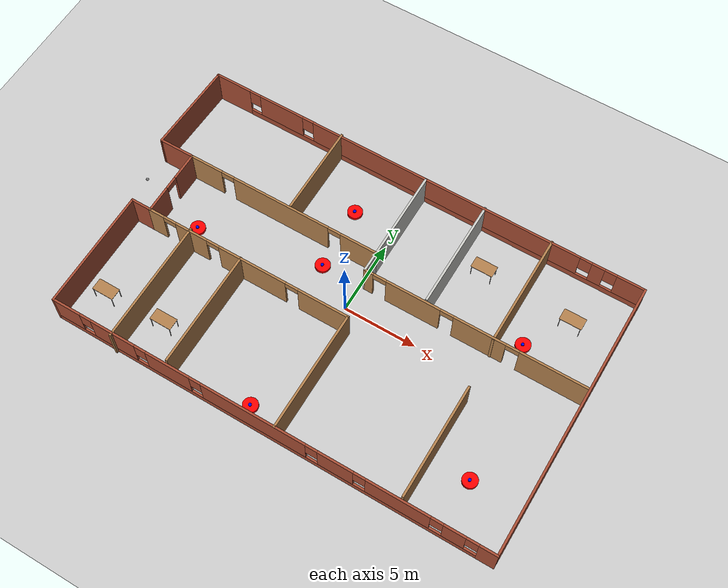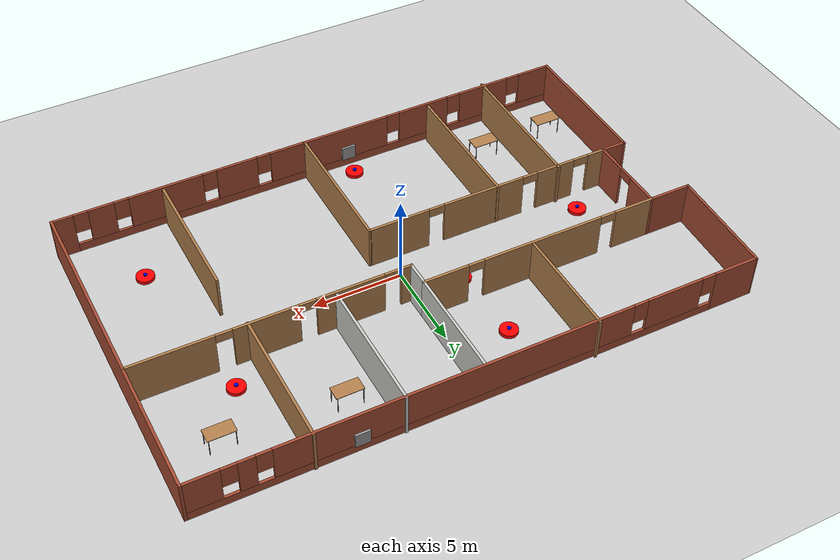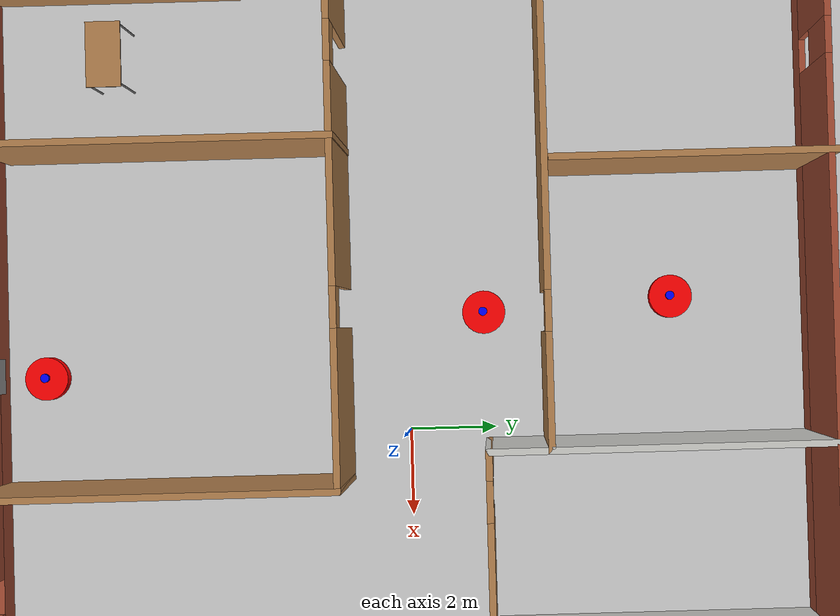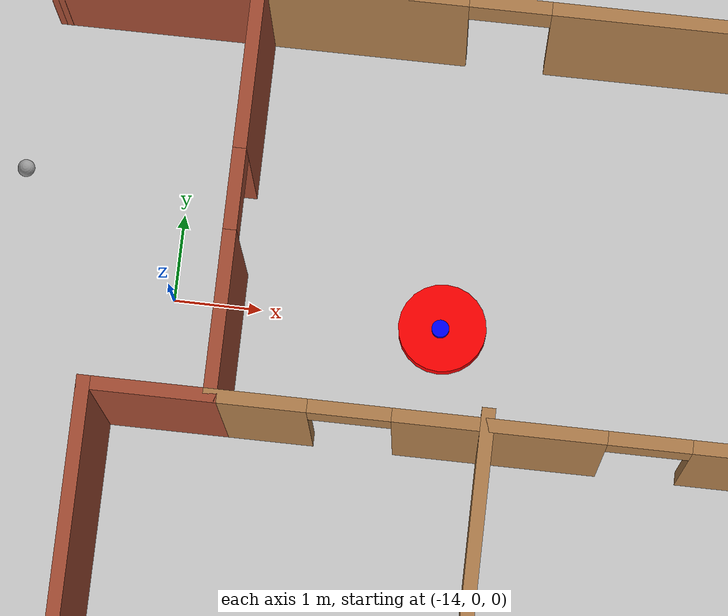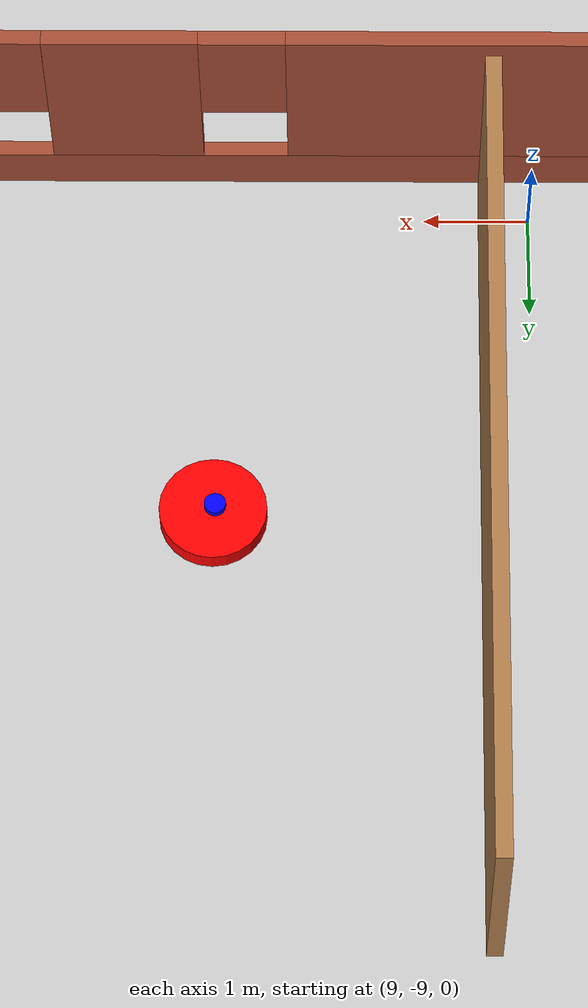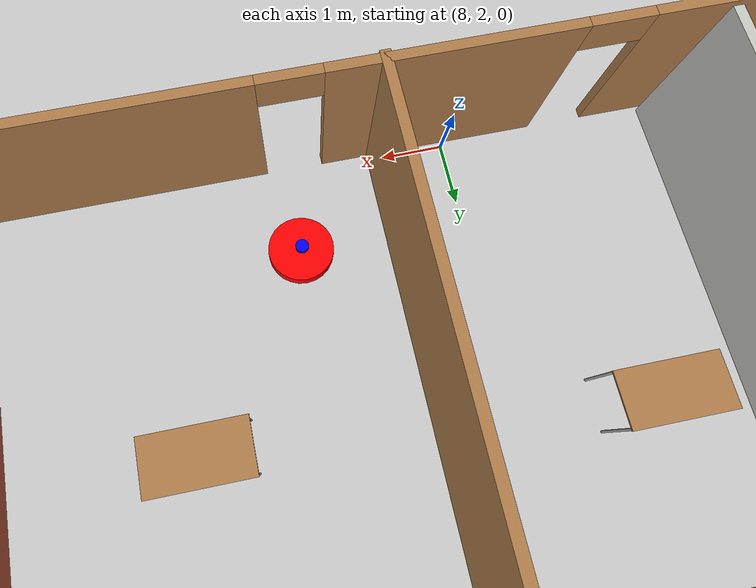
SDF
<sdf version="1.7">
 <world name="default">
  <plugin name="hello" filename="libhello.so"/>
  <model name="ground_plane">
   <static>1</static>
   <link name="link1">
    <collision name="collision">
     <geometry><plane><normal>0 0 1</normal><size>100 100</size></plane></geometry>
     <surface>
      <contact><collide_bitmask>65535</collide_bitmask></contact>
      <friction><ode><mu>100</mu><mu2>50</mu2></ode></friction>
     </surface>
    </collision>
    <visual name="visual">
     <cast_shadows>0</cast_shadows>
     <geometry><plane><normal>0 0 1</normal><size>100 100</size></plane></geometry>
     <material>
      <script><uri>file://media/materials/scripts/gazebo.material</uri><name>Gazebo/Grey</name></script>
     </material>
    </visual>
   </link>
  </model>
  <gravity>0 0 -9.8</gravity>
  <magnetic_field>6e-06 2.3e-05 -4.2e-05</magnetic_field>
  <atmosphere type="adiabatic"/>
  <physics type="ode">
   <max_step_size>0.001</max_step_size>
   <real_time_factor>1</real_time_factor>
   <real_time_update_rate>1000</real_time_update_rate>
  </physics>
  <scene><ambient>0.4 0.4 0.4 1</ambient><background>0.7 0.7 0.7 1</background><shadows>1</shadows></scene>
  <spherical_coordinates>
   <surface_model>EARTH_WGS84</surface_model>
   <latitude_deg>0</latitude_deg>
   <longitude_deg>0</longitude_deg>
   <elevation>0</elevation>
   <heading_deg>0</heading_deg>
  </spherical_coordinates>
  <model name="Floor_Plan">
   <pose>-0.077917 -0.10604 0 0 -0 0</pose>
   <link name="Wall_0">
    <pose>0.126492 9.44039 0 0 -0 0</pose>
    <visual name="Wall_0_Visual_0">
     <pose>-14.2048 0 1.25 0 -0 0</pose>
     <geometry><box><size>2.5905 0.15 2.5</size></box></geometry>
     <material>
      <script><uri>file://media/materials/scripts/gazebo.material</uri><name>Gazebo/Bricks</name></script>
      <ambient>1 1 1 1</ambient>
     </material>
     <meta><layer>0</layer></meta>
    </visual>
    <collision name="Wall_0_Collision_0">
     <geometry><box><size>2.5905 0.15 2.5</size></box></geometry>
     <pose>-14.2048 0 1.25 0 -0 0</pose>
    </collision>
    <visual name="Wall_0_Visual_1">
     <pose>1.29525 0 0.25 0 -0 0</pose>
     <geometry><box><size>28.4095 0.15 0.5</size></box></geometry>
     <material>
      <script><uri>file://media/materials/scripts/gazebo.material</uri><name>Gazebo/Bricks</name></script>
      <ambient>1 1 1 1</ambient>
     </material>
     <meta><layer>0</layer></meta>
    </visual>
    <collision name="Wall_0_Collision_1">
     <geometry><box><size>28.4095 0.15 0.5</size></box></geometry>
     <pose>1.29525 0 0.25 0 -0 0</pose>
    </collision>
    <visual name="Wall_0_Visual_2">
     <pose>-10.4857 0 1.5 0 -0 0</pose>
     <geometry><box><size>3.24758 0.15 2</size></box></geometry>
     <material>
      <script><uri>file://media/materials/scripts/gazebo.material</uri><name>Gazebo/Bricks</name></script>
      <ambient>1 1 1 1</ambient>
     </material>
     <meta><layer>0</layer></meta>
    </visual>
    <collision name="Wall_0_Collision_2">
     <geometry><box><size>3.24758 0.15 2</size></box></geometry>
     <pose>-10.4857 0 1.5 0 -0 0</pose>
    </collision>
    <visual name="Wall_0_Visual_3">
     <pose>1.51746 0 1.5 0 -0 0</pose>
     <geometry><box><size>19.1588 0.15 2</size></box></geometry>
     <material>
      <script><uri>file://media/materials/scripts/gazebo.material</uri><name>Gazebo/Bricks</name></script>
      <ambient>1 1 1 1</ambient>
     </material>
     <meta><layer>0</layer></meta>
    </visual>
    <collision name="Wall_0_Collision_3">
     <geometry><box><size>19.1588 0.15 2</size></box></geometry>
     <pose>1.51746 0 1.5 0 -0 0</pose>
    </collision>
    <visual name="Wall_0_Visual_4">
     <pose>12.3343 0 1.5 0 -0 0</pose>
     <geometry><box><size>0.874861 0.15 2</size></box></geometry>
     <material>
      <script><uri>file://media/materials/scripts/gazebo.material</uri><name>Gazebo/Bricks</name></script>
      <ambient>1 1 1 1</ambient>
     </material>
     <meta><layer>0</layer></meta>
    </visual>
    <collision name="Wall_0_Collision_4">
     <geometry><box><size>0.874861 0.15 2</size></box></geometry>
     <pose>12.3343 0 1.5 0 -0 0</pose>
    </collision>
    <visual name="Wall_0_Visual_5">
     <pose>14.5358 0 1.5 0 -0 0</pose>
     <geometry><box><size>1.9283 0.15 2</size></box></geometry>
     <material>
      <script><uri>file://media/materials/scripts/gazebo.material</uri><name>Gazebo/Bricks</name></script>
      <ambient>1 1 1 1</ambient>
     </material>
     <meta><layer>0</layer></meta>
    </visual>
    <collision name="Wall_0_Collision_5">
     <geometry><box><size>1.9283 0.15 2</size></box></geometry>
     <pose>14.5358 0 1.5 0 -0 0</pose>
    </collision>
    <visual name="Wall_0_Visual_6">
     <pose>-12.5095 0 1.9 0 -0 0</pose>
     <geometry><box><size>0.8 0.15 1.2</size></box></geometry>
     <material>
      <script><uri>file://media/materials/scripts/gazebo.material</uri><name>Gazebo/Bricks</name></script>
      <ambient>1 1 1 1</ambient>
     </material>
     <meta><layer>0</layer></meta>
    </visual>
    <collision name="Wall_0_Collision_6">
     <geometry><box><size>0.8 0.15 1.2</size></box></geometry>
     <pose>-12.5095 0 1.9 0 -0 0</pose>
    </collision>
    <visual name="Wall_0_Visual_7">
     <pose>-8.46192 0 1.9 0 -0 0</pose>
     <geometry><box><size>0.8 0.15 1.2</size></box></geometry>
     <material>
      <script><uri>file://media/materials/scripts/gazebo.material</uri><name>Gazebo/Bricks</name></script>
      <ambient>1 1 1 1</ambient>
     </material>
     <meta><layer>0</layer></meta>
    </visual>
    <collision name="Wall_0_Collision_7">
     <geometry><box><size>0.8 0.15 1.2</size></box></geometry>
     <pose>-8.46192 0 1.9 0 -0 0</pose>
    </collision>
    <visual name="Wall_0_Visual_8">
     <pose>11.4968 0 1.9 0 -0 0</pose>
     <geometry><box><size>0.8 0.15 1.2</size></box></geometry>
     <material>
      <script><uri>file://media/materials/scripts/gazebo.material</uri><name>Gazebo/Bricks</name></script>
      <ambient>1 1 1 1</ambient>
     </material>
     <meta><layer>0</layer></meta>
    </visual>
    <collision name="Wall_0_Collision_8">
     <geometry><box><size>0.8 0.15 1.2</size></box></geometry>
     <pose>11.4968 0 1.9 0 -0 0</pose>
    </collision>
    <visual name="Wall_0_Visual_9">
     <pose>13.1717 0 1.9 0 -0 0</pose>
     <geometry><box><size>0.8 0.15 1.2</size></box></geometry>
     <material>
      <script><uri>file://media/materials/scripts/gazebo.material</uri><name>Gazebo/Bricks</name></script>
      <ambient>1 1 1 1</ambient>
     </material>
     <meta><layer>0</layer></meta>
    </visual>
    <collision name="Wall_0_Collision_9">
     <geometry><box><size>0.8 0.15 1.2</size></box></geometry>
     <pose>13.1717 0 1.9 0 -0 0</pose>
    </collision>
   </link>
   <link name="Wall_1">
    <collision name="Wall_1_Collision">
     <geometry><box><size>19 0.15 2.5</size></box></geometry>
     <pose>0 0 1.25 0 -0 0</pose>
    </collision>
    <visual name="Wall_1_Visual">
     <pose>0 0 1.25 0 -0 0</pose>
     <geometry><box><size>19 0.15 2.5</size></box></geometry>
     <material>
      <script><uri>file://media/materials/scripts/gazebo.material</uri><name>Gazebo/Bricks</name></script>
      <ambient>1 1 1 1</ambient>
     </material>
     <meta><layer>0</layer></meta>
    </visual>
    <pose>15.5515 0.015393 0 0 -0 -1.5708</pose>
   </link>
   <link name="Wall_10">
    <collision name="Wall_10_Collision">
     <geometry><box><size>6.25 0.15 2.5</size></box></geometry>
     <pose>0 0 1.25 0 -0 0</pose>
    </collision>
    <visual name="Wall_10_Visual">
     <pose>0 0 1.25 0 -0 0</pose>
     <geometry><box><size>6.25 0.15 2.5</size></box></geometry>
     <material>
      <script><uri>file://media/materials/scripts/gazebo.material</uri><name>Gazebo/CeilingTiled</name></script>
      <ambient>1 1 1 1</ambient>
     </material>
     <meta><layer>0</layer></meta>
    </visual>
    <pose>0.401492 6.34039 0 0 -0 1.5708</pose>
   </link>
   <link name="Wall_12">
    <collision name="Wall_12_Collision">
     <geometry><box><size>6.25 0.15 2.5</size></box></geometry>
     <pose>0 0 1.25 0 -0 0</pose>
    </collision>
    <visual name="Wall_12_Visual">
     <pose>0 0 1.25 0 -0 0</pose>
     <geometry><box><size>6.25 0.15 2.5</size></box></geometry>
     <material>
      <script><uri>file://media/materials/scripts/gazebo.material</uri><name>Gazebo/Wood</name></script>
      <ambient>1 1 1 1</ambient>
     </material>
     <meta><layer>0</layer></meta>
    </visual>
    <pose>-5.86966 6.49851 0 0 -0 -1.5708</pose>
   </link>
   <link name="Wall_14">
    <collision name="Wall_14_Collision">
     <geometry><box><size>1.5 0.15 2.5</size></box></geometry>
     <pose>0 0 1.25 0 -0 0</pose>
    </collision>
    <visual name="Wall_14_Visual">
     <pose>0 0 1.25 0 -0 0</pose>
     <geometry><box><size>1.5 0.15 2.5</size></box></geometry>
     <material>
      <script><uri>file://media/materials/scripts/gazebo.material</uri><name>Gazebo/CeilingTiled</name></script>
      <ambient>1 1 1 1</ambient>
     </material>
     <meta><layer>0</layer></meta>
    </visual>
    <pose>0.401492 2.61539 0 0 -0 -1.5708</pose>
   </link>
   <link name="Wall_15">
    <pose>7.95149 1.94039 0 0 -0 0</pose>
    <visual name="Wall_15_Visual_0">
     <pose>-7.28606 0 1.25 0 -0 0</pose>
     <geometry><box><size>0.67788 0.15 2.5</size></box></geometry>
     <material>
      <script><uri>file://media/materials/scripts/gazebo.material</uri><name>Gazebo/Wood</name></script>
      <ambient>1 1 1 1</ambient>
     </material>
     <meta><layer>0</layer></meta>
    </visual>
    <collision name="Wall_15_Collision_0">
     <geometry><box><size>0.67788 0.15 2.5</size></box></geometry>
     <pose>-7.28606 0 1.25 0 -0 0</pose>
    </collision>
    <visual name="Wall_15_Visual_1">
     <pose>-4.17221 0 1.25 0 -0 0</pose>
     <geometry><box><size>3.74981 0.15 2.5</size></box></geometry>
     <material>
      <script><uri>file://media/materials/scripts/gazebo.material</uri><name>Gazebo/Wood</name></script>
      <ambient>1 1 1 1</ambient>
     </material>
     <meta><layer>0</layer></meta>
    </visual>
    <collision name="Wall_15_Collision_1">
     <geometry><box><size>3.74981 0.15 2.5</size></box></geometry>
     <pose>-4.17221 0 1.25 0 -0 0</pose>
    </collision>
    <visual name="Wall_15_Visual_2">
     <pose>0.357523 0 1.25 0 -0 0</pose>
     <geometry><box><size>3.50966 0.15 2.5</size></box></geometry>
     <material>
      <script><uri>file://media/materials/scripts/gazebo.material</uri><name>Gazebo/Wood</name></script>
      <ambient>1 1 1 1</ambient>
     </material>
     <meta><layer>0</layer></meta>
    </visual>
    <collision name="Wall_15_Collision_2">
     <geometry><box><size>3.50966 0.15 2.5</size></box></geometry>
     <pose>0.357523 0 1.25 0 -0 0</pose>
    </collision>
    <visual name="Wall_15_Visual_3">
     <pose>5.31868 0 1.25 0 -0 0</pose>
     <geometry><box><size>4.61265 0.15 2.5</size></box></geometry>
     <material>
      <script><uri>file://media/materials/scripts/gazebo.material</uri><name>Gazebo/Wood</name></script>
      <ambient>1 1 1 1</ambient>
     </material>
     <meta><layer>0</layer></meta>
    </visual>
    <collision name="Wall_15_Collision_3">
     <geometry><box><size>4.61265 0.15 2.5</size></box></geometry>
     <pose>5.31868 0 1.25 0 -0 0</pose>
    </collision>
    <visual name="Wall_15_Visual_4">
     <pose>-6.49712 0 2.25 0 -0 0</pose>
     <geometry><box><size>0.9 0.15 0.5</size></box></geometry>
     <material>
      <script><uri>file://media/materials/scripts/gazebo.material</uri><name>Gazebo/Wood</name></script>
      <ambient>1 1 1 1</ambient>
     </material>
     <meta><layer>0</layer></meta>
    </visual>
    <collision name="Wall_15_Collision_4">
     <geometry><box><size>0.9 0.15 0.5</size></box></geometry>
     <pose>-6.49712 0 2.25 0 -0 0</pose>
    </collision>
    <visual name="Wall_15_Visual_5">
     <pose>-1.84731 0 2.25 0 -0 0</pose>
     <geometry><box><size>0.9 0.15 0.5</size></box></geometry>
     <material>
      <script><uri>file://media/materials/scripts/gazebo.material</uri><name>Gazebo/Wood</name></script>
      <ambient>1 1 1 1</ambient>
     </material>
     <meta><layer>0</layer></meta>
    </visual>
    <collision name="Wall_15_Collision_5">
     <geometry><box><size>0.9 0.15 0.5</size></box></geometry>
     <pose>-1.84731 0 2.25 0 -0 0</pose>
    </collision>
    <visual name="Wall_15_Visual_6">
     <pose>2.56235 0 2.25 0 -0 0</pose>
     <geometry><box><size>0.9 0.15 0.5</size></box></geometry>
     <material>
      <script><uri>file://media/materials/scripts/gazebo.material</uri><name>Gazebo/Wood</name></script>
      <ambient>1 1 1 1</ambient>
     </material>
     <meta><layer>0</layer></meta>
    </visual>
    <collision name="Wall_15_Collision_6">
     <geometry><box><size>0.9 0.15 0.5</size></box></geometry>
     <pose>2.56235 0 2.25 0 -0 0</pose>
    </collision>
   </link>
   <link name="Wall_17">
    <collision name="Wall_17_Collision">
     <geometry><box><size>7.5 0.15 2.5</size></box></geometry>
     <pose>0 0 1.25 0 -0 0</pose>
    </collision>
    <visual name="Wall_17_Visual">
     <pose>0 0 1.25 0 -0 0</pose>
     <geometry><box><size>7.5 0.15 2.5</size></box></geometry>
     <material>
      <script><uri>file://media/materials/scripts/gazebo.material</uri><name>Gazebo/CeilingTiled</name></script>
      <ambient>1 1 1 1</ambient>
     </material>
     <meta><layer>0</layer></meta>
    </visual>
    <pose>4.59822 5.82699 0 0 -0 -1.5708</pose>
   </link>
   <link name="Wall_19">
    <collision name="Wall_19_Collision">
     <geometry><box><size>7.75 0.15 2.5</size></box></geometry>
     <pose>0 0 1.25 0 -0 0</pose>
    </collision>
    <visual name="Wall_19_Visual">
     <pose>0 0 1.25 0 -0 0</pose>
     <geometry><box><size>7.75 0.15 2.5</size></box></geometry>
     <material>
      <script><uri>file://media/materials/scripts/gazebo.material</uri><name>Gazebo/Wood</name></script>
      <ambient>1 1 1 1</ambient>
     </material>
     <meta><layer>0</layer></meta>
    </visual>
    <pose>9.25061 5.70199 0 0 -0 -1.5708</pose>
   </link>
   <link name="Wall_2">
    <pose>0.501492 -9.40961 0 0 -0 3.14159</pose>
    <visual name="Wall_2_Visual_0">
     <pose>-14.52 0 1.25 0 -0 0</pose>
     <geometry><box><size>1.21002 0.15 2.5</size></box></geometry>
     <material>
      <script><uri>file://media/materials/scripts/gazebo.material</uri><name>Gazebo/Bricks</name></script>
      <ambient>1 1 1 1</ambient>
     </material>
     <meta><layer>0</layer></meta>
    </visual>
    <collision name="Wall_2_Collision_0">
     <geometry><box><size>1.21002 0.15 2.5</size></box></geometry>
     <pose>-14.52 0 1.25 0 -0 0</pose>
    </collision>
    <visual name="Wall_2_Visual_1">
     <pose>0.605012 0 0.25 0 -0 0</pose>
     <geometry><box><size>29.04 0.15 0.5</size></box></geometry>
     <material>
      <script><uri>file://media/materials/scripts/gazebo.material</uri><name>Gazebo/Bricks</name></script>
      <ambient>1 1 1 1</ambient>
     </material>
     <meta><layer>0</layer></meta>
    </visual>
    <collision name="Wall_2_Collision_1">
     <geometry><box><size>29.04 0.15 0.5</size></box></geometry>
     <pose>0.605012 0 0.25 0 -0 0</pose>
    </collision>
    <visual name="Wall_2_Visual_2">
     <pose>-12.3984 0 1.5 0 -0 0</pose>
     <geometry><box><size>1.43315 0.15 2</size></box></geometry>
     <material>
      <script><uri>file://media/materials/scripts/gazebo.material</uri><name>Gazebo/Bricks</name></script>
      <ambient>1 1 1 1</ambient>
     </material>
     <meta><layer>0</layer></meta>
    </visual>
    <collision name="Wall_2_Collision_2">
     <geometry><box><size>1.43315 0.15 2</size></box></geometry>
     <pose>-12.3984 0 1.5 0 -0 0</pose>
    </collision>
    <visual name="Wall_2_Visual_3">
     <pose>-8.7928 0 1.5 0 -0 0</pose>
     <geometry><box><size>4.17806 0.15 2</size></box></geometry>
     <material>
      <script><uri>file://media/materials/scripts/gazebo.material</uri><name>Gazebo/Bricks</name></script>
      <ambient>1 1 1 1</ambient>
     </material>
     <meta><layer>0</layer></meta>
    </visual>
    <collision name="Wall_2_Collision_3">
     <geometry><box><size>4.17806 0.15 2</size></box></geometry>
     <pose>-8.7928 0 1.5 0 -0 0</pose>
    </collision>
    <visual name="Wall_2_Visual_4">
     <pose>-4.72196 0 1.5 0 -0 0</pose>
     <geometry><box><size>2.36363 0.15 2</size></box></geometry>
     <material>
      <script><uri>file://media/materials/scripts/gazebo.material</uri><name>Gazebo/Bricks</name></script>
      <ambient>1 1 1 1</ambient>
     </material>
     <meta><layer>0</layer></meta>
    </visual>
    <collision name="Wall_2_Collision_4">
     <geometry><box><size>2.36363 0.15 2</size></box></geometry>
     <pose>-4.72196 0 1.5 0 -0 0</pose>
    </collision>
    <visual name="Wall_2_Visual_5">
     <pose>0.837652 0 1.5 0 -0 0</pose>
     <geometry><box><size>7.15559 0.15 2</size></box></geometry>
     <material>
      <script><uri>file://media/materials/scripts/gazebo.material</uri><name>Gazebo/Bricks</name></script>
      <ambient>1 1 1 1</ambient>
     </material>
     <meta><layer>0</layer></meta>
    </visual>
    <collision name="Wall_2_Collision_5">
     <geometry><box><size>7.15559 0.15 2</size></box></geometry>
     <pose>0.837652 0 1.5 0 -0 0</pose>
    </collision>
    <visual name="Wall_2_Visual_6">
     <pose>6.76945 0 1.5 0 -0 0</pose>
     <geometry><box><size>3.10801 0.15 2</size></box></geometry>
     <material>
      <script><uri>file://media/materials/scripts/gazebo.material</uri><name>Gazebo/Bricks</name></script>
      <ambient>1 1 1 1</ambient>
     </material>
     <meta><layer>0</layer></meta>
    </visual>
    <collision name="Wall_2_Collision_6">
     <geometry><box><size>3.10801 0.15 2</size></box></geometry>
     <pose>6.76945 0 1.5 0 -0 0</pose>
    </collision>
    <visual name="Wall_2_Visual_7">
     <pose>10.7007 0 1.5 0 -0 0</pose>
     <geometry><box><size>3.15453 0.15 2</size></box></geometry>
     <material>
      <script><uri>file://media/materials/scripts/gazebo.material</uri><name>Gazebo/Bricks</name></script>
      <ambient>1 1 1 1</ambient>
     </material>
     <meta><layer>0</layer></meta>
    </visual>
    <collision name="Wall_2_Collision_7">
     <geometry><box><size>3.15453 0.15 2</size></box></geometry>
     <pose>10.7007 0 1.5 0 -0 0</pose>
    </collision>
    <visual name="Wall_2_Visual_8">
     <pose>14.1015 0 1.5 0 -0 0</pose>
     <geometry><box><size>2.04701 0.15 2</size></box></geometry>
     <material>
      <script><uri>file://media/materials/scripts/gazebo.material</uri><name>Gazebo/Bricks</name></script>
      <ambient>1 1 1 1</ambient>
     </material>
     <meta><layer>0</layer></meta>
    </visual>
    <collision name="Wall_2_Collision_8">
     <geometry><box><size>2.04701 0.15 2</size></box></geometry>
     <pose>14.1015 0 1.5 0 -0 0</pose>
    </collision>
    <visual name="Wall_2_Visual_9">
     <pose>-13.515 0 1.9 0 -0 0</pose>
     <geometry><box><size>0.8 0.15 1.2</size></box></geometry>
     <material>
      <script><uri>file://media/materials/scripts/gazebo.material</uri><name>Gazebo/Bricks</name></script>
      <ambient>1 1 1 1</ambient>
     </material>
     <meta><layer>0</layer></meta>
    </visual>
    <collision name="Wall_2_Collision_9">
     <geometry><box><size>0.8 0.15 1.2</size></box></geometry>
     <pose>-13.515 0 1.9 0 -0 0</pose>
    </collision>
    <visual name="Wall_2_Visual_10">
     <pose>-11.2818 0 1.9 0 -0 0</pose>
     <geometry><box><size>0.8 0.15 1.2</size></box></geometry>
     <material>
      <script><uri>file://media/materials/scripts/gazebo.material</uri><name>Gazebo/Bricks</name></script>
      <ambient>1 1 1 1</ambient>
     </material>
     <meta><layer>0</layer></meta>
    </visual>
    <collision name="Wall_2_Collision_10">
     <geometry><box><size>0.8 0.15 1.2</size></box></geometry>
     <pose>-11.2818 0 1.9 0 -0 0</pose>
    </collision>
    <visual name="Wall_2_Visual_11">
     <pose>-6.30377 0 1.9 0 -0 0</pose>
     <geometry><box><size>0.8 0.15 1.2</size></box></geometry>
     <material>
      <script><uri>file://media/materials/scripts/gazebo.material</uri><name>Gazebo/Bricks</name></script>
      <ambient>1 1 1 1</ambient>
     </material>
     <meta><layer>0</layer></meta>
    </visual>
    <collision name="Wall_2_Collision_11">
     <geometry><box><size>0.8 0.15 1.2</size></box></geometry>
     <pose>-6.30377 0 1.9 0 -0 0</pose>
    </collision>
    <visual name="Wall_2_Visual_12">
     <pose>-3.14014 0 1.9 0 -0 0</pose>
     <geometry><box><size>0.8 0.15 1.2</size></box></geometry>
     <material>
      <script><uri>file://media/materials/scripts/gazebo.material</uri><name>Gazebo/Bricks</name></script>
      <ambient>1 1 1 1</ambient>
     </material>
     <meta><layer>0</layer></meta>
    </visual>
    <collision name="Wall_2_Collision_12">
     <geometry><box><size>0.8 0.15 1.2</size></box></geometry>
     <pose>-3.14014 0 1.9 0 -0 0</pose>
    </collision>
    <visual name="Wall_2_Visual_13">
     <pose>4.81545 0 1.9 0 -0 0</pose>
     <geometry><box><size>0.8 0.15 1.2</size></box></geometry>
     <material>
      <script><uri>file://media/materials/scripts/gazebo.material</uri><name>Gazebo/Bricks</name></script>
      <ambient>1 1 1 1</ambient>
     </material>
     <meta><layer>0</layer></meta>
    </visual>
    <collision name="Wall_2_Collision_13">
     <geometry><box><size>0.8 0.15 1.2</size></box></geometry>
     <pose>4.81545 0 1.9 0 -0 0</pose>
    </collision>
    <visual name="Wall_2_Visual_14">
     <pose>8.72346 0 1.9 0 -0 0</pose>
     <geometry><box><size>0.8 0.15 1.2</size></box></geometry>
     <material>
      <script><uri>file://media/materials/scripts/gazebo.material</uri><name>Gazebo/Bricks</name></script>
      <ambient>1 1 1 1</ambient>
     </material>
     <meta><layer>0</layer></meta>
    </visual>
    <collision name="Wall_2_Collision_14">
     <geometry><box><size>0.8 0.15 1.2</size></box></geometry>
     <pose>8.72346 0 1.9 0 -0 0</pose>
    </collision>
    <visual name="Wall_2_Visual_15">
     <pose>12.678 0 1.9 0 -0 0</pose>
     <geometry><box><size>0.8 0.15 1.2</size></box></geometry>
     <material>
      <script><uri>file://media/materials/scripts/gazebo.material</uri><name>Gazebo/Bricks</name></script>
      <ambient>1 1 1 1</ambient>
     </material>
     <meta><layer>0</layer></meta>
    </visual>
    <collision name="Wall_2_Collision_15">
     <geometry><box><size>0.8 0.15 1.2</size></box></geometry>
     <pose>12.678 0 1.9 0 -0 0</pose>
    </collision>
   </link>
   <link name="Wall_21">
    <pose>-6.02351 -1.30961 0 0 -0 0</pose>
    <visual name="Wall_21_Visual_0">
     <pose>-6.69387 0 1.25 0 -0 0</pose>
     <geometry><box><size>1.11225 0.15 2.5</size></box></geometry>
     <material>
      <script><uri>file://media/materials/scripts/gazebo.material</uri><name>Gazebo/Wood</name></script>
      <ambient>1 0.764706 0.305882 1</ambient>
     </material>
     <meta><layer>0</layer></meta>
    </visual>
    <collision name="Wall_21_Collision_0">
     <geometry><box><size>1.11225 0.15 2.5</size></box></geometry>
     <pose>-6.69387 0 1.25 0 -0 0</pose>
    </collision>
    <visual name="Wall_21_Visual_1">
     <pose>-4.08716 0 1.25 0 -0 0</pose>
     <geometry><box><size>2.30118 0.15 2.5</size></box></geometry>
     <material>
      <script><uri>file://media/materials/scripts/gazebo.material</uri><name>Gazebo/Wood</name></script>
      <ambient>1 0.764706 0.305882 1</ambient>
     </material>
     <meta><layer>0</layer></meta>
    </visual>
    <collision name="Wall_21_Collision_1">
     <geometry><box><size>2.30118 0.15 2.5</size></box></geometry>
     <pose>-4.08716 0 1.25 0 -0 0</pose>
    </collision>
    <visual name="Wall_21_Visual_2">
     <pose>0.374652 0 1.25 0 -0 0</pose>
     <geometry><box><size>4.82244 0.15 2.5</size></box></geometry>
     <material>
      <script><uri>file://media/materials/scripts/gazebo.material</uri><name>Gazebo/Wood</name></script>
      <ambient>1 0.764706 0.305882 1</ambient>
     </material>
     <meta><layer>0</layer></meta>
    </visual>
    <collision name="Wall_21_Collision_2">
     <geometry><box><size>4.82244 0.15 2.5</size></box></geometry>
     <pose>0.374652 0 1.25 0 -0 0</pose>
    </collision>
    <visual name="Wall_21_Visual_3">
     <pose>5.46794 0 1.25 0 -0 0</pose>
     <geometry><box><size>3.56413 0.15 2.5</size></box></geometry>
     <material>
      <script><uri>file://media/materials/scripts/gazebo.material</uri><name>Gazebo/Wood</name></script>
      <ambient>1 0.764706 0.305882 1</ambient>
     </material>
     <meta><layer>0</layer></meta>
    </visual>
    <collision name="Wall_21_Collision_3">
     <geometry><box><size>3.56413 0.15 2.5</size></box></geometry>
     <pose>5.46794 0 1.25 0 -0 0</pose>
    </collision>
    <visual name="Wall_21_Visual_4">
     <pose>-5.68775 0 2.25 0 -0 0</pose>
     <geometry><box><size>0.9 0.15 0.5</size></box></geometry>
     <material>
      <script><uri>file://media/materials/scripts/gazebo.material</uri><name>Gazebo/Wood</name></script>
      <ambient>1 0.764706 0.305882 1</ambient>
     </material>
     <meta><layer>0</layer></meta>
    </visual>
    <collision name="Wall_21_Collision_4">
     <geometry><box><size>0.9 0.15 0.5</size></box></geometry>
     <pose>-5.68775 0 2.25 0 -0 0</pose>
    </collision>
    <visual name="Wall_21_Visual_5">
     <pose>-2.48657 0 2.25 0 -0 0</pose>
     <geometry><box><size>0.9 0.15 0.5</size></box></geometry>
     <material>
      <script><uri>file://media/materials/scripts/gazebo.material</uri><name>Gazebo/Wood</name></script>
      <ambient>1 0.764706 0.305882 1</ambient>
     </material>
     <meta><layer>0</layer></meta>
    </visual>
    <collision name="Wall_21_Collision_5">
     <geometry><box><size>0.9 0.15 0.5</size></box></geometry>
     <pose>-2.48657 0 2.25 0 -0 0</pose>
    </collision>
    <visual name="Wall_21_Visual_6">
     <pose>3.23587 0 2.25 0 -0 0</pose>
     <geometry><box><size>0.9 0.15 0.5</size></box></geometry>
     <material>
      <script><uri>file://media/materials/scripts/gazebo.material</uri><name>Gazebo/Wood</name></script>
      <ambient>1 0.764706 0.305882 1</ambient>
     </material>
     <meta><layer>0</layer></meta>
    </visual>
    <collision name="Wall_21_Collision_6">
     <geometry><box><size>0.9 0.15 0.5</size></box></geometry>
     <pose>3.23587 0 2.25 0 -0 0</pose>
    </collision>
   </link>
   <link name="Wall_22">
    <collision name="Wall_22_Collision">
     <geometry><box><size>8.25 0.15 2.5</size></box></geometry>
     <pose>0 0 1.25 0 -0 0</pose>
    </collision>
    <visual name="Wall_22_Visual">
     <pose>0 0 1.25 0 -0 0</pose>
     <geometry><box><size>8.25 0.15 2.5</size></box></geometry>
     <material>
      <script><uri>file://media/materials/scripts/gazebo.material</uri><name>Gazebo/Wood</name></script>
      <ambient>1 0.764706 0.305882 1</ambient>
     </material>
     <meta><layer>0</layer></meta>
    </visual>
    <pose>1.15149 -5.35961 0 0 -0 -1.5708</pose>
   </link>
   <link name="Wall_24">
    <collision name="Wall_24_Collision">
     <geometry><box><size>8 0.15 2.5</size></box></geometry>
     <pose>0 0 1.25 0 -0 0</pose>
    </collision>
    <visual name="Wall_24_Visual">
     <pose>0 0 1.25 0 -0 0</pose>
     <geometry><box><size>8 0.15 2.5</size></box></geometry>
     <material>
      <script><uri>file://media/materials/scripts/gazebo.material</uri><name>Gazebo/Wood</name></script>
      <ambient>1 0.764706 0.305882 1</ambient>
     </material>
     <meta><layer>0</layer></meta>
    </visual>
    <pose>-6.47447 -5.21656 0 0 -0 -1.5708</pose>
   </link>
   <link name="Wall_26">
    <collision name="Wall_26_Collision">
     <geometry><box><size>8.5 0.15 2.5</size></box></geometry>
     <pose>0 0 1.25 0 -0 0</pose>
    </collision>
    <visual name="Wall_26_Visual">
     <pose>0 0 1.25 0 -0 0</pose>
     <geometry><box><size>8.5 0.15 2.5</size></box></geometry>
     <material>
      <script><uri>file://media/materials/scripts/gazebo.material</uri><name>Gazebo/Wood</name></script>
      <ambient>1 1 1 1</ambient>
     </material>
     <meta><layer>0</layer></meta>
    </visual>
    <pose>-10.2429 -5.37351 0 0 -0 -1.5708</pose>
   </link>
   <link name="Wall_28">
    <collision name="Wall_28_Collision">
     <geometry><box><size>7.75 0.15 2.5</size></box></geometry>
     <pose>0 0 1.25 0 -0 0</pose>
    </collision>
    <visual name="Wall_28_Visual">
     <pose>0 0 1.25 0 -0 0</pose>
     <geometry><box><size>7.75 0.15 2.5</size></box></geometry>
     <material>
      <script><uri>file://media/materials/scripts/gazebo.material</uri><name>Gazebo/Wood</name></script>
      <ambient>1 1 1 1</ambient>
     </material>
     <meta><layer>0</layer></meta>
    </visual>
    <pose>9.48323 -5.3541 0 0 -0 1.5708</pose>
   </link>
   <link name="Wall_3">
    <collision name="Wall_3_Collision">
     <geometry><box><size>8.25 0.15 2.5</size></box></geometry>
     <pose>0 0 1.25 0 -0 0</pose>
    </collision>
    <visual name="Wall_3_Visual">
     <pose>0 0 1.25 0 -0 0</pose>
     <geometry><box><size>8.25 0.15 2.5</size></box></geometry>
     <material>
      <script><uri>file://media/materials/scripts/gazebo.material</uri><name>Gazebo/Bricks</name></script>
      <ambient>1 1 1 1</ambient>
     </material>
     <meta><layer>0</layer></meta>
    </visual>
    <pose>-14.5485 -5.35961 0 0 -0 1.5708</pose>
   </link>
   <link name="Wall_4">
    <collision name="Wall_4_Collision">
     <geometry><box><size>1.5 0.15 2.5</size></box></geometry>
     <pose>0 0 1.25 0 -0 0</pose>
    </collision>
    <visual name="Wall_4_Visual">
     <pose>0 0 1.25 0 -0 0</pose>
     <geometry><box><size>1.5 0.15 2.5</size></box></geometry>
     <material>
      <script><uri>file://media/materials/scripts/gazebo.material</uri><name>Gazebo/Bricks</name></script>
      <ambient>1 1 1 1</ambient>
     </material>
     <meta><layer>0</layer></meta>
    </visual>
    <pose>-13.8735 -1.30961 0 0 -0 0</pose>
   </link>
   <link name="Wall_5">
    <pose>-13.1985 0.990393 0 0 -0 1.5708</pose>
    <visual name="Wall_5_Visual_0">
     <pose>-1.43617 0 1.25 0 -0 0</pose>
     <geometry><box><size>1.87766 0.15 2.5</size></box></geometry>
     <material>
      <script><uri>file://media/materials/scripts/gazebo.material</uri><name>Gazebo/Bricks</name></script>
      <ambient>1 1 1 1</ambient>
     </material>
     <meta><layer>0</layer></meta>
    </visual>
    <collision name="Wall_5_Collision_0">
     <geometry><box><size>1.87766 0.15 2.5</size></box></geometry>
     <pose>-1.43617 0 1.25 0 -0 0</pose>
    </collision>
    <visual name="Wall_5_Visual_1">
     <pose>1.38883 0 1.25 0 -0 0</pose>
     <geometry><box><size>1.97234 0.15 2.5</size></box></geometry>
     <material>
      <script><uri>file://media/materials/scripts/gazebo.material</uri><name>Gazebo/Bricks</name></script>
      <ambient>1 1 1 1</ambient>
     </material>
     <meta><layer>0</layer></meta>
    </visual>
    <collision name="Wall_5_Collision_1">
     <geometry><box><size>1.97234 0.15 2.5</size></box></geometry>
     <pose>1.38883 0 1.25 0 -0 0</pose>
    </collision>
    <visual name="Wall_5_Visual_2">
     <pose>-0.047338 0 2.25 0 -0 0</pose>
     <geometry><box><size>0.9 0.15 0.5</size></box></geometry>
     <material>
      <script><uri>file://media/materials/scripts/gazebo.material</uri><name>Gazebo/Bricks</name></script>
      <ambient>1 1 1 1</ambient>
     </material>
     <meta><layer>0</layer></meta>
    </visual>
    <collision name="Wall_5_Collision_2">
     <geometry><box><size>0.9 0.15 0.5</size></box></geometry>
     <pose>-0.047338 0 2.25 0 -0 0</pose>
    </collision>
   </link>
   <link name="Wall_6">
    <collision name="Wall_6_Collision">
     <geometry><box><size>2.5 0.15 2.5</size></box></geometry>
     <pose>0 0 1.25 0 -0 0</pose>
    </collision>
    <visual name="Wall_6_Visual">
     <pose>0 0 1.25 0 -0 0</pose>
     <geometry><box><size>2.5 0.15 2.5</size></box></geometry>
     <material>
      <script><uri>file://media/materials/scripts/gazebo.material</uri><name>Gazebo/Bricks</name></script>
      <ambient>1 1 1 1</ambient>
     </material>
     <meta><layer>0</layer></meta>
    </visual>
    <pose>-14.3735 3.29039 0 0 -0 3.14159</pose>
   </link>
   <link name="Wall_7">
    <collision name="Wall_7_Collision">
     <geometry><box><size>6.30508 0.15 2.5</size></box></geometry>
     <pose>0 0 1.25 0 -0 0</pose>
    </collision>
    <visual name="Wall_7_Visual">
     <pose>0 0 1.25 0 -0 0</pose>
     <geometry><box><size>6.30508 0.15 2.5</size></box></geometry>
     <material>
      <script><uri>file://media/materials/scripts/gazebo.material</uri><name>Gazebo/Bricks</name></script>
      <ambient>1 1 1 1</ambient>
     </material>
     <meta><layer>0</layer></meta>
    </visual>
    <pose>-15.4235 6.36539 0 0 -0 1.53017</pose>
   </link>
   <link name="Wall_9">
    <pose>-6.39851 3.29039 0 0 -0 0</pose>
    <visual name="Wall_9_Visual_0">
     <pose>-5.69451 0 1.25 0 -0 0</pose>
     <geometry><box><size>2.36099 0.15 2.5</size></box></geometry>
     <material>
      <script><uri>file://media/materials/scripts/gazebo.material</uri><name>Gazebo/Wood</name></script>
      <ambient>1 1 1 1</ambient>
     </material>
     <meta><layer>0</layer></meta>
    </visual>
    <collision name="Wall_9_Collision_0">
     <geometry><box><size>2.36099 0.15 2.5</size></box></geometry>
     <pose>-5.69451 0 1.25 0 -0 0</pose>
    </collision>
    <visual name="Wall_9_Visual_1">
     <pose>-0.12718 0 1.25 0 -0 0</pose>
     <geometry><box><size>6.97366 0.15 2.5</size></box></geometry>
     <material>
      <script><uri>file://media/materials/scripts/gazebo.material</uri><name>Gazebo/Wood</name></script>
      <ambient>1 1 1 1</ambient>
     </material>
     <meta><layer>0</layer></meta>
    </visual>
    <collision name="Wall_9_Collision_1">
     <geometry><box><size>6.97366 0.15 2.5</size></box></geometry>
     <pose>-0.12718 0 1.25 0 -0 0</pose>
    </collision>
    <visual name="Wall_9_Visual_2">
     <pose>5.56733 0 1.25 0 -0 0</pose>
     <geometry><box><size>2.61535 0.15 2.5</size></box></geometry>
     <material>
      <script><uri>file://media/materials/scripts/gazebo.material</uri><name>Gazebo/Wood</name></script>
      <ambient>1 1 1 1</ambient>
     </material>
     <meta><layer>0</layer></meta>
    </visual>
    <collision name="Wall_9_Collision_2">
     <geometry><box><size>2.61535 0.15 2.5</size></box></geometry>
     <pose>5.56733 0 1.25 0 -0 0</pose>
    </collision>
    <visual name="Wall_9_Visual_3">
     <pose>-4.06401 0 2.25 0 -0 0</pose>
     <geometry><box><size>0.9 0.15 0.5</size></box></geometry>
     <material>
      <script><uri>file://media/materials/scripts/gazebo.material</uri><name>Gazebo/Wood</name></script>
      <ambient>1 1 1 1</ambient>
     </material>
     <meta><layer>0</layer></meta>
    </visual>
    <collision name="Wall_9_Collision_3">
     <geometry><box><size>0.9 0.15 0.5</size></box></geometry>
     <pose>-4.06401 0 2.25 0 -0 0</pose>
    </collision>
    <visual name="Wall_9_Visual_4">
     <pose>3.80965 0 2.25 0 -0 0</pose>
     <geometry><box><size>0.9 0.15 0.5</size></box></geometry>
     <material>
      <script><uri>file://media/materials/scripts/gazebo.material</uri><name>Gazebo/Wood</name></script>
      <ambient>1 1 1 1</ambient>
     </material>
     <meta><layer>0</layer></meta>
    </visual>
    <collision name="Wall_9_Collision_4">
     <geometry><box><size>0.9 0.15 0.5</size></box></geometry>
     <pose>3.80965 0 2.25 0 -0 0</pose>
    </collision>
   </link>
   <link name="Window_10">
    <collision name="Window_10_Collision">
     <geometry><box><size>0.8 0.17 0.8</size></box></geometry>
     <pose>0 0 0.4 0 -0 0</pose>
    </collision>
    <visual name="Window_10_Visual">
     <pose>0 0 0.4 0 -0 0</pose>
     <geometry><box><size>0.8 0.17 0.8</size></box></geometry>
     <material>
      <script><uri>file://media/materials/scripts/gazebo.material</uri><name>Gazebo/Grey</name></script>
     </material>
    </visual>
    <pose>-1.42947 -9.29221 0.5 0 -0 0</pose>
   </link>
   <link name="Window_2">
    <collision name="Window_2_Collision">
     <geometry><box><size>0.8 0.17 0.8</size></box></geometry>
     <pose>0 0 0.4 0 -0 0</pose>
    </collision>
    <visual name="Window_2_Visual">
     <pose>0 0 0.4 0 -0 0</pose>
     <geometry><box><size>0.8 0.17 0.8</size></box></geometry>
     <material>
      <script><uri>file://media/materials/scripts/gazebo.material</uri><name>Gazebo/Grey</name></script>
     </material>
    </visual>
    <pose>6.87789 9.54851 0.5 0 -0 0</pose>
   </link>
   <static>1</static>
  </model>
  <light name="sun" type="directional">
   <pose>-16.1005 32.6646 10 0 -0 0</pose>
   <diffuse>0.8 0.8 0.8 1</diffuse>
   <specular>0.2 0.2 0.2 1</specular>
   <attenuation>
    <range>1000</range>
    <constant>0.9</constant>
    <linear>0.01</linear>
    <quadratic>0.001</quadratic>
   </attenuation>
   <direction>-0.5 0.1 -0.9</direction>
   <spot><inner_angle>0</inner_angle><outer_angle>0</outer_angle><falloff>0</falloff></spot>
  </light>
  <model name="Table">
   <static>1</static>
   <link name="link">
    <collision name="surface">
     <pose>0 0 1 0 -0 0</pose>
     <geometry><box><size>1.5 0.8 0.03</size></box></geometry>
     <surface><friction><ode><mu>0.6</mu><mu2>0.6</mu2></ode></friction></surface>
    </collision>
    <visual name="visual1">
     <pose>0 0 1 0 -0 0</pose>
     <geometry><box><size>1.5 0.8 0.03</size></box></geometry>
     <material>
      <diffuse>1 1 1 1</diffuse>
      <script><uri>file://media/materials/scripts/gazebo.material</uri><name>Gazebo/Wood</name></script>
      <pbr>
       <metal>
        <albedo_map>https://fuel.ignitionrobotics.org/1.0/openrobotics/models/table/3/files/Table_Diffuse.jpg</albedo_map>
       </metal>
      </pbr>
     </material>
    </visual>
    <collision name="front_left_leg">
     <pose>0.68 0.38 0.5 0 -0 0</pose>
     <geometry><cylinder><radius>0.02</radius><length>1</length></cylinder></geometry>
    </collision>
    <visual name="front_left_leg">
     <pose>0.68 0.38 0.5 0 -0 0</pose>
     <geometry><cylinder><radius>0.02</radius><length>1</length></cylinder></geometry>
     <material>
      <diffuse>0.5 0.5 0.5 1</diffuse>
      <script><uri>file://media/materials/scripts/gazebo.material</uri><name>Gazebo/Grey</name></script>
     </material>
    </visual>
    <collision name="front_right_leg">
     <pose>0.68 -0.38 0.5 0 -0 0</pose>
     <geometry><cylinder><radius>0.02</radius><length>1</length></cylinder></geometry>
    </collision>
    <visual name="front_right_leg">
     <pose>0.68 -0.38 0.5 0 -0 0</pose>
     <geometry><cylinder><radius>0.02</radius><length>1</length></cylinder></geometry>
     <material>
      <diffuse>0.5 0.5 0.5 1</diffuse>
      <script><uri>file://media/materials/scripts/gazebo.material</uri><name>Gazebo/Grey</name></script>
     </material>
    </visual>
    <collision name="back_right_leg">
     <pose>-0.68 -0.38 0.5 0 -0 0</pose>
     <geometry><cylinder><radius>0.02</radius><length>1</length></cylinder></geometry>
    </collision>
    <visual name="back_right_leg">
     <pose>-0.68 -0.38 0.5 0 -0 0</pose>
     <geometry><cylinder><radius>0.02</radius><length>1</length></cylinder></geometry>
     <material>
      <diffuse>0.5 0.5 0.5 1</diffuse>
      <script><uri>file://media/materials/scripts/gazebo.material</uri><name>Gazebo/Grey</name></script>
     </material>
    </visual>
    <collision name="back_left_leg">
     <pose>-0.68 0.38 0.5 0 -0 0</pose>
     <geometry><cylinder><radius>0.02</radius><length>1</length></cylinder></geometry>
    </collision>
    <visual name="back_left_leg">
     <pose>-0.68 0.38 0.5 0 -0 0</pose>
     <geometry><cylinder><radius>0.02</radius><length>1</length></cylinder></geometry>
     <material>
      <diffuse>0.5 0.5 0.5 1</diffuse>
      <script><uri>file://media/materials/scripts/gazebo.material</uri><name>Gazebo/Grey</name></script>
     </material>
    </visual>
   </link>
   <pose>12.5058 6.11591 0 0 -0 0</pose>
  </model>
  <model name="Table_clone">
   <static>1</static>
   <link name="link">
    <collision name="surface">
     <pose>0 0 1 0 -0 0</pose>
     <geometry><box><size>1.5 0.8 0.03</size></box></geometry>
     <surface><friction><ode><mu>0.6</mu><mu2>0.6</mu2></ode></friction></surface>
    </collision>
    <visual name="visual1">
     <pose>0 0 1 0 -0 0</pose>
     <geometry><box><size>1.5 0.8 0.03</size></box></geometry>
     <material>
      <diffuse>1 1 1 1</diffuse>
      <script><uri>file://media/materials/scripts/gazebo.material</uri><name>Gazebo/Wood</name></script>
      <pbr>
       <metal>
        <albedo_map>https://fuel.ignitionrobotics.org/1.0/openrobotics/models/table/3/files/Table_Diffuse.jpg</albedo_map>
       </metal>
      </pbr>
     </material>
    </visual>
    <collision name="front_left_leg">
     <pose>0.68 0.38 0.5 0 -0 0</pose>
     <geometry><cylinder><radius>0.02</radius><length>1</length></cylinder></geometry>
    </collision>
    <visual name="front_left_leg">
     <pose>0.68 0.38 0.5 0 -0 0</pose>
     <geometry><cylinder><radius>0.02</radius><length>1</length></cylinder></geometry>
     <material>
      <diffuse>0.5 0.5 0.5 1</diffuse>
      <script><uri>file://media/materials/scripts/gazebo.material</uri><name>Gazebo/Grey</name></script>
     </material>
    </visual>
    <collision name="front_right_leg">
     <pose>0.68 -0.38 0.5 0 -0 0</pose>
     <geometry><cylinder><radius>0.02</radius><length>1</length></cylinder></geometry>
    </collision>
    <visual name="front_right_leg">
     <pose>0.68 -0.38 0.5 0 -0 0</pose>
     <geometry><cylinder><radius>0.02</radius><length>1</length></cylinder></geometry>
     <material>
      <diffuse>0.5 0.5 0.5 1</diffuse>
      <script><uri>file://media/materials/scripts/gazebo.material</uri><name>Gazebo/Grey</name></script>
     </material>
    </visual>
    <collision name="back_right_leg">
     <pose>-0.68 -0.38 0.5 0 -0 0</pose>
     <geometry><cylinder><radius>0.02</radius><length>1</length></cylinder></geometry>
    </collision>
    <visual name="back_right_leg">
     <pose>-0.68 -0.38 0.5 0 -0 0</pose>
     <geometry><cylinder><radius>0.02</radius><length>1</length></cylinder></geometry>
     <material>
      <diffuse>0.5 0.5 0.5 1</diffuse>
      <script><uri>file://media/materials/scripts/gazebo.material</uri><name>Gazebo/Grey</name></script>
     </material>
    </visual>
    <collision name="back_left_leg">
     <pose>-0.68 0.38 0.5 0 -0 0</pose>
     <geometry><cylinder><radius>0.02</radius><length>1</length></cylinder></geometry>
    </collision>
    <visual name="back_left_leg">
     <pose>-0.68 0.38 0.5 0 -0 0</pose>
     <geometry><cylinder><radius>0.02</radius><length>1</length></cylinder></geometry>
     <material>
      <diffuse>0.5 0.5 0.5 1</diffuse>
      <script><uri>file://media/materials/scripts/gazebo.material</uri><name>Gazebo/Grey</name></script>
     </material>
    </visual>
   </link>
   <pose>6.17799 6.51368 0 0 -0 0</pose>
  </model>
  <model name="Table_clone_0">
   <static>1</static>
   <link name="link">
    <collision name="surface">
     <pose>0 0 1 0 -0 0</pose>
     <geometry><box><size>1.5 0.8 0.03</size></box></geometry>
     <surface><friction><ode><mu>0.6</mu><mu2>0.6</mu2></ode></friction></surface>
    </collision>
    <visual name="visual1">
     <pose>0 0 1 0 -0 0</pose>
     <geometry><box><size>1.5 0.8 0.03</size></box></geometry>
     <material>
      <diffuse>1 1 1 1</diffuse>
      <script><uri>file://media/materials/scripts/gazebo.material</uri><name>Gazebo/Wood</name></script>
      <pbr>
       <metal>
        <albedo_map>https://fuel.ignitionrobotics.org/1.0/openrobotics/models/table/3/files/Table_Diffuse.jpg</albedo_map>
       </metal>
      </pbr>
     </material>
    </visual>
    <collision name="front_left_leg">
     <pose>0.68 0.38 0.5 0 -0 0</pose>
     <geometry><cylinder><radius>0.02</radius><length>1</length></cylinder></geometry>
    </collision>
    <visual name="front_left_leg">
     <pose>0.68 0.38 0.5 0 -0 0</pose>
     <geometry><cylinder><radius>0.02</radius><length>1</length></cylinder></geometry>
     <material>
      <diffuse>0.5 0.5 0.5 1</diffuse>
      <script><uri>file://media/materials/scripts/gazebo.material</uri><name>Gazebo/Grey</name></script>
     </material>
    </visual>
    <collision name="front_right_leg">
     <pose>0.68 -0.38 0.5 0 -0 0</pose>
     <geometry><cylinder><radius>0.02</radius><length>1</length></cylinder></geometry>
    </collision>
    <visual name="front_right_leg">
     <pose>0.68 -0.38 0.5 0 -0 0</pose>
     <geometry><cylinder><radius>0.02</radius><length>1</length></cylinder></geometry>
     <material>
      <diffuse>0.5 0.5 0.5 1</diffuse>
      <script><uri>file://media/materials/scripts/gazebo.material</uri><name>Gazebo/Grey</name></script>
     </material>
    </visual>
    <collision name="back_right_leg">
     <pose>-0.68 -0.38 0.5 0 -0 0</pose>
     <geometry><cylinder><radius>0.02</radius><length>1</length></cylinder></geometry>
    </collision>
    <visual name="back_right_leg">
     <pose>-0.68 -0.38 0.5 0 -0 0</pose>
     <geometry><cylinder><radius>0.02</radius><length>1</length></cylinder></geometry>
     <material>
      <diffuse>0.5 0.5 0.5 1</diffuse>
      <script><uri>file://media/materials/scripts/gazebo.material</uri><name>Gazebo/Grey</name></script>
     </material>
    </visual>
    <collision name="back_left_leg">
     <pose>-0.68 0.38 0.5 0 -0 0</pose>
     <geometry><cylinder><radius>0.02</radius><length>1</length></cylinder></geometry>
    </collision>
    <visual name="back_left_leg">
     <pose>-0.68 0.38 0.5 0 -0 0</pose>
     <geometry><cylinder><radius>0.02</radius><length>1</length></cylinder></geometry>
     <material>
      <diffuse>0.5 0.5 0.5 1</diffuse>
      <script><uri>file://media/materials/scripts/gazebo.material</uri><name>Gazebo/Grey</name></script>
     </material>
    </visual>
   </link>
   <pose>-8.79511 -6.71924 0 0 -0 0</pose>
  </model>
  <model name="Table_clone_1">
   <static>1</static>
   <link name="link">
    <collision name="surface">
     <pose>0 0 1 0 -0 0</pose>
     <geometry><box><size>1.5 0.8 0.03</size></box></geometry>
     <surface><friction><ode><mu>0.6</mu><mu2>0.6</mu2></ode></friction></surface>
    </collision>
    <visual name="visual1">
     <pose>0 0 1 0 -0 0</pose>
     <geometry><box><size>1.5 0.8 0.03</size></box></geometry>
     <material>
      <diffuse>1 1 1 1</diffuse>
      <script><uri>file://media/materials/scripts/gazebo.material</uri><name>Gazebo/Wood</name></script>
      <pbr>
       <metal>
        <albedo_map>https://fuel.ignitionrobotics.org/1.0/openrobotics/models/table/3/files/Table_Diffuse.jpg</albedo_map>
       </metal>
      </pbr>
     </material>
    </visual>
    <collision name="front_left_leg">
     <pose>0.68 0.38 0.5 0 -0 0</pose>
     <geometry><cylinder><radius>0.02</radius><length>1</length></cylinder></geometry>
    </collision>
    <visual name="front_left_leg">
     <pose>0.68 0.38 0.5 0 -0 0</pose>
     <geometry><cylinder><radius>0.02</radius><length>1</length></cylinder></geometry>
     <material>
      <diffuse>0.5 0.5 0.5 1</diffuse>
      <script><uri>file://media/materials/scripts/gazebo.material</uri><name>Gazebo/Grey</name></script>
     </material>
    </visual>
    <collision name="front_right_leg">
     <pose>0.68 -0.38 0.5 0 -0 0</pose>
     <geometry><cylinder><radius>0.02</radius><length>1</length></cylinder></geometry>
    </collision>
    <visual name="front_right_leg">
     <pose>0.68 -0.38 0.5 0 -0 0</pose>
     <geometry><cylinder><radius>0.02</radius><length>1</length></cylinder></geometry>
     <material>
      <diffuse>0.5 0.5 0.5 1</diffuse>
      <script><uri>file://media/materials/scripts/gazebo.material</uri><name>Gazebo/Grey</name></script>
     </material>
    </visual>
    <collision name="back_right_leg">
     <pose>-0.68 -0.38 0.5 0 -0 0</pose>
     <geometry><cylinder><radius>0.02</radius><length>1</length></cylinder></geometry>
    </collision>
    <visual name="back_right_leg">
     <pose>-0.68 -0.38 0.5 0 -0 0</pose>
     <geometry><cylinder><radius>0.02</radius><length>1</length></cylinder></geometry>
     <material>
      <diffuse>0.5 0.5 0.5 1</diffuse>
      <script><uri>file://media/materials/scripts/gazebo.material</uri><name>Gazebo/Grey</name></script>
     </material>
    </visual>
    <collision name="back_left_leg">
     <pose>-0.68 0.38 0.5 0 -0 0</pose>
     <geometry><cylinder><radius>0.02</radius><length>1</length></cylinder></geometry>
    </collision>
    <visual name="back_left_leg">
     <pose>-0.68 0.38 0.5 0 -0 0</pose>
     <geometry><cylinder><radius>0.02</radius><length>1</length></cylinder></geometry>
     <material>
      <diffuse>0.5 0.5 0.5 1</diffuse>
      <script><uri>file://media/materials/scripts/gazebo.material</uri><name>Gazebo/Grey</name></script>
     </material>
    </visual>
   </link>
   <pose>-12.9968 -6.86813 0 0 -0 0</pose>
  </model>
  <model name="Vacuum_Cleaning_Robot_clone">
   <link name="link_0">
    <inertial>
     <mass>1</mass>
     <inertia><ixx>0.145833</ixx><ixy>0</ixy><ixz>0</ixz><iyy>0.145833</iyy><iyz>0</iyz><izz>0.125</izz></inertia>
    </inertial>
    <pose>-0.031267 0.111986 0.08 0 -0 0</pose>
    <visual name="visual">
     <geometry><cylinder><radius>0.5</radius><length>0.2</length></cylinder></geometry>
     <material>
      <lighting>1</lighting>
      <script><uri>file://media/materials/scripts/gazebo.material</uri><name>Gazebo/Grey</name></script>
      <shader type="pixel"><normal_map>__default__</normal_map></shader>
      <ambient>1 0 0 1</ambient>
      <diffuse>1 0 0 1</diffuse>
      <specular>1 0 0 1</specular>
      <emissive>1 0 0 1</emissive>
     </material>
    </visual>
    <collision name="collision">
     <geometry><cylinder><radius>0.5</radius><length>0.2</length></cylinder></geometry>
     <surface>
      <friction>
       <ode><mu>1</mu><mu2>1</mu2><fdir1>0 0 0</fdir1><slip1>0</slip1><slip2>0</slip2></ode>
       <torsional>
        <coefficient>1</coefficient>
        <patch_radius>0</patch_radius>
        <surface_radius>0</surface_radius>
        <use_patch_radius>1</use_patch_radius>
        <ode><slip>0</slip></ode>
       </torsional>
      </friction>
      <bounce><restitution_coefficient>0</restitution_coefficient><threshold>1e+06</threshold></bounce>
      <contact>
       <collide_without_contact>0</collide_without_contact>
       <collide_without_contact_bitmask>1</collide_without_contact_bitmask>
       <collide_bitmask>1</collide_bitmask>
       <ode>
        <soft_cfm>0</soft_cfm>
        <soft_erp>0.2</soft_erp>
        <kp>1e+13</kp>
        <kd>1</kd>
        <max_vel>0.01</max_vel>
        <min_depth>0</min_depth>
       </ode>
       <bullet>
        <split_impulse>1</split_impulse>
        <split_impulse_penetration_threshold>-0.01</split_impulse_penetration_threshold>
        <soft_cfm>0</soft_cfm>
        <soft_erp>0.2</soft_erp>
        <kp>1e+13</kp>
        <kd>1</kd>
       </bullet>
      </contact>
     </surface>
    </collision>
   </link>
   <link name="link_0_0">
    <inertial>
     <mass>1</mass>
     <inertia><ixx>0.145833</ixx><ixy>0</ixy><ixz>0</ixz><iyy>0.145833</iyy><iyz>0</iyz><izz>0.125</izz></inertia>
    </inertial>
    <pose>-0.051205 0.091924 0.2 0 -0 0.00312</pose>
    <visual name="visual">
     <geometry><cylinder><radius>0.1</radius><length>0.1</length></cylinder></geometry>
     <material>
      <lighting>1</lighting>
      <script><uri>file://media/materials/scripts/gazebo.material</uri><name>Gazebo/Grey</name></script>
      <shader type="pixel"><normal_map>__default__</normal_map></shader>
      <ambient>0 0 1 1</ambient>
      <diffuse>0 0 1 1</diffuse>
      <specular>0 0 1 1</specular>
      <emissive>0 0 0 1</emissive>
     </material>
    </visual>
    <collision name="collision">
     <geometry><cylinder><radius>0.1</radius><length>0.1</length></cylinder></geometry>
     <surface>
      <friction>
       <ode><mu>1</mu><mu2>1</mu2><fdir1>0 0 0</fdir1><slip1>0</slip1><slip2>0</slip2></ode>
       <torsional>
        <coefficient>1</coefficient>
        <patch_radius>0</patch_radius>
        <surface_radius>0</surface_radius>
        <use_patch_radius>1</use_patch_radius>
        <ode><slip>0</slip></ode>
       </torsional>
      </friction>
      <bounce><restitution_coefficient>0</restitution_coefficient><threshold>1e+06</threshold></bounce>
      <contact>
       <collide_without_contact>0</collide_without_contact>
       <collide_without_contact_bitmask>1</collide_without_contact_bitmask>
       <collide_bitmask>1</collide_bitmask>
       <ode>
        <soft_cfm>0</soft_cfm>
        <soft_erp>0.2</soft_erp>
        <kp>1e+13</kp>
        <kd>1</kd>
        <max_vel>0.01</max_vel>
        <min_depth>0</min_depth>
       </ode>
       <bullet>
        <split_impulse>1</split_impulse>
        <split_impulse_penetration_threshold>-0.01</split_impulse_penetration_threshold>
        <soft_cfm>0</soft_cfm>
        <soft_erp>0.2</soft_erp>
        <kp>1e+13</kp>
        <kd>1</kd>
       </bullet>
      </contact>
     </surface>
    </collision>
   </link>
   <link name="link_2">
    <inertial>
     <mass>1</mass>
     <inertia><ixx>0.1</ixx><ixy>0</ixy><ixz>0</ixz><iyy>0.1</iyy><iyz>0</iyz><izz>0.1</izz></inertia>
    </inertial>
    <pose>0.318733 0.111986 -0.02 0 -0 0</pose>
    <visual name="visual">
     <geometry><sphere><radius>0.1</radius></sphere></geometry>
     <material>
      <lighting>1</lighting>
      <script><uri>file://media/materials/scripts/gazebo.material</uri><name>Gazebo/Grey</name></script>
      <shader type="pixel"><normal_map>__default__</normal_map></shader>
      <ambient>0.3 0.3 1 1</ambient>
      <diffuse>0.7 0.7 1 1</diffuse>
      <specular>0.01 0.01 1 1</specular>
      <emissive>0 0 1 1</emissive>
     </material>
    </visual>
    <collision name="collision">
     <geometry><sphere><radius>0.1</radius></sphere></geometry>
     <surface>
      <friction>
       <ode><mu>1</mu><mu2>1</mu2><fdir1>0 0 0</fdir1><slip1>0</slip1><slip2>0</slip2></ode>
       <torsional>
        <coefficient>1</coefficient>
        <patch_radius>0</patch_radius>
        <surface_radius>0</surface_radius>
        <use_patch_radius>1</use_patch_radius>
        <ode><slip>0</slip></ode>
       </torsional>
      </friction>
      <bounce><restitution_coefficient>0</restitution_coefficient><threshold>1e+06</threshold></bounce>
      <contact>
       <collide_without_contact>0</collide_without_contact>
       <collide_without_contact_bitmask>1</collide_without_contact_bitmask>
       <collide_bitmask>1</collide_bitmask>
       <ode>
        <soft_cfm>0</soft_cfm>
        <soft_erp>0.2</soft_erp>
        <kp>1e+13</kp>
        <kd>1</kd>
        <max_vel>0.01</max_vel>
        <min_depth>0</min_depth>
       </ode>
       <bullet>
        <split_impulse>1</split_impulse>
        <split_impulse_penetration_threshold>-0.01</split_impulse_penetration_threshold>
        <soft_cfm>0</soft_cfm>
        <soft_erp>0.2</soft_erp>
        <kp>1e+13</kp>
        <kd>1</kd>
       </bullet>
      </contact>
     </surface>
    </collision>
   </link>
   <link name="link_2_clone">
    <inertial>
     <mass>1</mass>
     <inertia><ixx>0.1</ixx><ixy>0</ixy><ixz>0</ixz><iyy>0.1</iyy><iyz>0</iyz><izz>0.1</izz></inertia>
    </inertial>
    <pose>-0.381267 0.111986 -0.02 0 -0 0</pose>
    <visual name="visual">
     <geometry><sphere><radius>0.1</radius></sphere></geometry>
     <material>
      <lighting>1</lighting>
      <script><uri>file://media/materials/scripts/gazebo.material</uri><name>Gazebo/Grey</name></script>
      <shader type="pixel"><normal_map>__default__</normal_map></shader>
      <ambient>0.3 0.3 1 1</ambient>
      <diffuse>0.7 0.7 1 1</diffuse>
      <specular>0.01 0.01 1 1</specular>
      <emissive>0 0 0 1</emissive>
     </material>
    </visual>
    <collision name="collision">
     <geometry><sphere><radius>0.1</radius></sphere></geometry>
     <surface>
      <friction>
       <ode><mu>1</mu><mu2>1</mu2><fdir1>0 0 0</fdir1><slip1>0</slip1><slip2>0</slip2></ode>
       <torsional>
        <coefficient>1</coefficient>
        <patch_radius>0</patch_radius>
        <surface_radius>0</surface_radius>
        <use_patch_radius>1</use_patch_radius>
        <ode><slip>0</slip></ode>
       </torsional>
      </friction>
      <bounce><restitution_coefficient>0</restitution_coefficient><threshold>1e+06</threshold></bounce>
      <contact>
       <collide_without_contact>0</collide_without_contact>
       <collide_without_contact_bitmask>1</collide_without_contact_bitmask>
       <collide_bitmask>1</collide_bitmask>
       <ode>
        <soft_cfm>0</soft_cfm>
        <soft_erp>0.2</soft_erp>
        <kp>1e+13</kp>
        <kd>1</kd>
        <max_vel>0.01</max_vel>
        <min_depth>0</min_depth>
       </ode>
       <bullet>
        <split_impulse>1</split_impulse>
        <split_impulse_penetration_threshold>-0.01</split_impulse_penetration_threshold>
        <soft_cfm>0</soft_cfm>
        <soft_erp>0.2</soft_erp>
        <kp>1e+13</kp>
        <kd>1</kd>
       </bullet>
      </contact>
     </surface>
    </collision>
   </link>
   <link name="link_2_clone_0">
    <inertial>
     <mass>1</mass>
     <inertia><ixx>0.1</ixx><ixy>0</ixy><ixz>0</ixz><iyy>0.1</iyy><iyz>0</iyz><izz>0.1</izz></inertia>
    </inertial>
    <pose>-0.031267 -0.238014 -0.02 0 -0 0</pose>
    <visual name="visual">
     <geometry><sphere><radius>0.1</radius></sphere></geometry>
     <material>
      <lighting>1</lighting>
      <script><uri>file://media/materials/scripts/gazebo.material</uri><name>Gazebo/Grey</name></script>
      <shader type="pixel"><normal_map>__default__</normal_map></shader>
      <ambient>0.3 0.3 1 1</ambient>
      <diffuse>0.7 0.7 1 1</diffuse>
      <specular>0.01 0.01 1 1</specular>
      <emissive>0 0 0 1</emissive>
     </material>
    </visual>
    <collision name="collision">
     <geometry><sphere><radius>0.1</radius></sphere></geometry>
     <surface>
      <friction>
       <ode><mu>1</mu><mu2>1</mu2><fdir1>0 0 0</fdir1><slip1>0</slip1><slip2>0</slip2></ode>
       <torsional>
        <coefficient>1</coefficient>
        <patch_radius>0</patch_radius>
        <surface_radius>0</surface_radius>
        <use_patch_radius>1</use_patch_radius>
        <ode><slip>0</slip></ode>
       </torsional>
      </friction>
      <bounce><restitution_coefficient>0</restitution_coefficient><threshold>1e+06</threshold></bounce>
      <contact>
       <collide_without_contact>0</collide_without_contact>
       <collide_without_contact_bitmask>1</collide_without_contact_bitmask>
       <collide_bitmask>1</collide_bitmask>
       <ode>
        <soft_cfm>0</soft_cfm>
        <soft_erp>0.2</soft_erp>
        <kp>1e+13</kp>
        <kd>1</kd>
        <max_vel>0.01</max_vel>
        <min_depth>0</min_depth>
       </ode>
       <bullet>
        <split_impulse>1</split_impulse>
        <split_impulse_penetration_threshold>-0.01</split_impulse_penetration_threshold>
        <soft_cfm>0</soft_cfm>
        <soft_erp>0.2</soft_erp>
        <kp>1e+13</kp>
        <kd>1</kd>
       </bullet>
      </contact>
     </surface>
    </collision>
   </link>
   <link name="link_2_clone_1">
    <inertial>
     <mass>1</mass>
     <inertia><ixx>0.1</ixx><ixy>0</ixy><ixz>0</ixz><iyy>0.1</iyy><iyz>0</iyz><izz>0.1</izz></inertia>
    </inertial>
    <pose>-0.031267 0.461986 -0.02 0 -0 0</pose>
    <visual name="visual">
     <geometry><sphere><radius>0.1</radius></sphere></geometry>
     <material>
      <lighting>1</lighting>
      <script><uri>file://media/materials/scripts/gazebo.material</uri><name>Gazebo/Grey</name></script>
      <shader type="pixel"><normal_map>__default__</normal_map></shader>
      <ambient>0.3 0.3 1 1</ambient>
      <diffuse>0.7 0.7 1 1</diffuse>
      <specular>0.01 0.01 1 1</specular>
      <emissive>0 0 0 1</emissive>
     </material>
    </visual>
    <collision name="collision">
     <geometry><sphere><radius>0.1</radius></sphere></geometry>
     <surface>
      <friction>
       <ode><mu>1</mu><mu2>1</mu2><fdir1>0 0 0</fdir1><slip1>0</slip1><slip2>0</slip2></ode>
       <torsional>
        <coefficient>1</coefficient>
        <patch_radius>0</patch_radius>
        <surface_radius>0</surface_radius>
        <use_patch_radius>1</use_patch_radius>
        <ode><slip>0</slip></ode>
       </torsional>
      </friction>
      <bounce><restitution_coefficient>0</restitution_coefficient><threshold>1e+06</threshold></bounce>
      <contact>
       <collide_without_contact>0</collide_without_contact>
       <collide_without_contact_bitmask>1</collide_without_contact_bitmask>
       <collide_bitmask>1</collide_bitmask>
       <ode>
        <soft_cfm>0</soft_cfm>
        <soft_erp>0.2</soft_erp>
        <kp>1e+13</kp>
        <kd>1</kd>
        <max_vel>0.01</max_vel>
        <min_depth>0</min_depth>
       </ode>
       <bullet>
        <split_impulse>1</split_impulse>
        <split_impulse_penetration_threshold>-0.01</split_impulse_penetration_threshold>
        <soft_cfm>0</soft_cfm>
        <soft_erp>0.2</soft_erp>
        <kp>1e+13</kp>
        <kd>1</kd>
       </bullet>
      </contact>
     </surface>
    </collision>
   </link>
   <joint name="link_0_JOINT_0" type="revolute">
    <parent>link_0</parent>
    <child>link_0_0</child>
    <axis>
     <xyz>0 0 1</xyz>
     <limit>
      <lower>-1.79769e+308</lower>
      <upper>1.79769e+308</upper>
      <effort>-1</effort>
      <velocity>-1</velocity>
     </limit>
     <dynamics>
      <spring_reference>0</spring_reference>
      <spring_stiffness>0</spring_stiffness>
      <damping>0</damping>
      <friction>0</friction>
     </dynamics>
    </axis>
    <physics>
     <ode><limit><cfm>0</cfm><erp>0.2</erp></limit><suspension><cfm>0</cfm><erp>0.2</erp></suspension></ode>
    </physics>
   </joint>
   <joint name="link_0_JOINT_1" type="revolute">
    <parent>link_0</parent>
    <child>link_2</child>
    <axis>
     <xyz>1 0 0</xyz>
     <limit>
      <lower>-1.79769e+308</lower>
      <upper>1.79769e+308</upper>
      <effort>-1</effort>
      <velocity>-1</velocity>
     </limit>
     <dynamics>
      <spring_reference>0</spring_reference>
      <spring_stiffness>0</spring_stiffness>
      <damping>0</damping>
      <friction>0</friction>
     </dynamics>
    </axis>
    <physics>
     <ode><limit><cfm>0</cfm><erp>0.2</erp></limit><suspension><cfm>0</cfm><erp>0.2</erp></suspension></ode>
    </physics>
   </joint>
   <joint name="link_0_JOINT_2" type="revolute">
    <parent>link_0</parent>
    <child>link_2_clone</child>
    <axis>
     <xyz>1 0 0</xyz>
     <limit>
      <lower>-1.79769e+308</lower>
      <upper>1.79769e+308</upper>
      <effort>-1</effort>
      <velocity>-1</velocity>
     </limit>
     <dynamics>
      <spring_reference>0</spring_reference>
      <spring_stiffness>0</spring_stiffness>
      <damping>0</damping>
      <friction>0</friction>
     </dynamics>
    </axis>
    <physics>
     <ode><limit><cfm>0</cfm><erp>0.2</erp></limit><suspension><cfm>0</cfm><erp>0.2</erp></suspension></ode>
    </physics>
   </joint>
   <joint name="link_0_JOINT_3" type="revolute">
    <parent>link_0</parent>
    <child>link_2_clone_0</child>
    <axis>
     <xyz>1 0 0</xyz>
     <limit>
      <lower>-1.79769e+308</lower>
      <upper>1.79769e+308</upper>
      <effort>-1</effort>
      <velocity>-1</velocity>
     </limit>
     <dynamics>
      <spring_reference>0</spring_reference>
      <spring_stiffness>0</spring_stiffness>
      <damping>0</damping>
      <friction>0</friction>
     </dynamics>
    </axis>
    <physics>
     <ode><limit><cfm>0</cfm><erp>0.2</erp></limit><suspension><cfm>0</cfm><erp>0.2</erp></suspension></ode>
    </physics>
   </joint>
   <joint name="link_0_JOINT_4" type="revolute">
    <parent>link_0</parent>
    <child>link_2_clone_1</child>
    <axis>
     <xyz>1 0 0</xyz>
     <limit>
      <lower>-1.79769e+308</lower>
      <upper>1.79769e+308</upper>
      <effort>-1</effort>
      <velocity>-1</velocity>
     </limit>
     <dynamics>
      <spring_reference>0</spring_reference>
      <spring_stiffness>0</spring_stiffness>
      <damping>0</damping>
      <friction>0</friction>
     </dynamics>
    </axis>
    <physics>
     <ode><limit><cfm>0</cfm><erp>0.2</erp></limit><suspension><cfm>0</cfm><erp>0.2</erp></suspension></ode>
    </physics>
   </joint>
   <static>0</static>
   <pose>11.9924 -5.92064 0.120001 -1e-06 1e-06 -0.001857</pose>
  </model>
  <model name="Vacuum_Cleaning_Robot_clone_0">
   <link name="link_0">
    <inertial>
     <mass>1</mass>
     <inertia><ixx>0.145833</ixx><ixy>0</ixy><ixz>0</ixz><iyy>0.145833</iyy><iyz>0</iyz><izz>0.125</izz></inertia>
    </inertial>
    <pose>-0.031267 0.111986 0.08 0 -0 0</pose>
    <visual name="visual">
     <geometry><cylinder><radius>0.5</radius><length>0.2</length></cylinder></geometry>
     <material>
      <lighting>1</lighting>
      <script><uri>file://media/materials/scripts/gazebo.material</uri><name>Gazebo/Grey</name></script>
      <shader type="pixel"><normal_map>__default__</normal_map></shader>
      <ambient>1 0 0 1</ambient>
      <diffuse>1 0 0 1</diffuse>
      <specular>1 0 0 1</specular>
      <emissive>1 0 0 1</emissive>
     </material>
    </visual>
    <collision name="collision">
     <geometry><cylinder><radius>0.5</radius><length>0.2</length></cylinder></geometry>
     <surface>
      <friction>
       <ode><mu>1</mu><mu2>1</mu2><fdir1>0 0 0</fdir1><slip1>0</slip1><slip2>0</slip2></ode>
       <torsional>
        <coefficient>1</coefficient>
        <patch_radius>0</patch_radius>
        <surface_radius>0</surface_radius>
        <use_patch_radius>1</use_patch_radius>
        <ode><slip>0</slip></ode>
       </torsional>
      </friction>
      <bounce><restitution_coefficient>0</restitution_coefficient><threshold>1e+06</threshold></bounce>
      <contact>
       <collide_without_contact>0</collide_without_contact>
       <collide_without_contact_bitmask>1</collide_without_contact_bitmask>
       <collide_bitmask>1</collide_bitmask>
       <ode>
        <soft_cfm>0</soft_cfm>
        <soft_erp>0.2</soft_erp>
        <kp>1e+13</kp>
        <kd>1</kd>
        <max_vel>0.01</max_vel>
        <min_depth>0</min_depth>
       </ode>
       <bullet>
        <split_impulse>1</split_impulse>
        <split_impulse_penetration_threshold>-0.01</split_impulse_penetration_threshold>
        <soft_cfm>0</soft_cfm>
        <soft_erp>0.2</soft_erp>
        <kp>1e+13</kp>
        <kd>1</kd>
       </bullet>
      </contact>
     </surface>
    </collision>
   </link>
   <link name="link_0_0">
    <inertial>
     <mass>1</mass>
     <inertia><ixx>0.145833</ixx><ixy>0</ixy><ixz>0</ixz><iyy>0.145833</iyy><iyz>0</iyz><izz>0.125</izz></inertia>
    </inertial>
    <pose>-0.051205 0.091924 0.2 0 -0 0.00312</pose>
    <visual name="visual">
     <geometry><cylinder><radius>0.1</radius><length>0.1</length></cylinder></geometry>
     <material>
      <lighting>1</lighting>
      <script><uri>file://media/materials/scripts/gazebo.material</uri><name>Gazebo/Grey</name></script>
      <shader type="pixel"><normal_map>__default__</normal_map></shader>
      <ambient>0 0 1 1</ambient>
      <diffuse>0 0 1 1</diffuse>
      <specular>0 0 1 1</specular>
      <emissive>0 0 0 1</emissive>
     </material>
    </visual>
    <collision name="collision">
     <geometry><cylinder><radius>0.1</radius><length>0.1</length></cylinder></geometry>
     <surface>
      <friction>
       <ode><mu>1</mu><mu2>1</mu2><fdir1>0 0 0</fdir1><slip1>0</slip1><slip2>0</slip2></ode>
       <torsional>
        <coefficient>1</coefficient>
        <patch_radius>0</patch_radius>
        <surface_radius>0</surface_radius>
        <use_patch_radius>1</use_patch_radius>
        <ode><slip>0</slip></ode>
       </torsional>
      </friction>
      <bounce><restitution_coefficient>0</restitution_coefficient><threshold>1e+06</threshold></bounce>
      <contact>
       <collide_without_contact>0</collide_without_contact>
       <collide_without_contact_bitmask>1</collide_without_contact_bitmask>
       <collide_bitmask>1</collide_bitmask>
       <ode>
        <soft_cfm>0</soft_cfm>
        <soft_erp>0.2</soft_erp>
        <kp>1e+13</kp>
        <kd>1</kd>
        <max_vel>0.01</max_vel>
        <min_depth>0</min_depth>
       </ode>
       <bullet>
        <split_impulse>1</split_impulse>
        <split_impulse_penetration_threshold>-0.01</split_impulse_penetration_threshold>
        <soft_cfm>0</soft_cfm>
        <soft_erp>0.2</soft_erp>
        <kp>1e+13</kp>
        <kd>1</kd>
       </bullet>
      </contact>
     </surface>
    </collision>
   </link>
   <link name="link_2">
    <inertial>
     <mass>1</mass>
     <inertia><ixx>0.1</ixx><ixy>0</ixy><ixz>0</ixz><iyy>0.1</iyy><iyz>0</iyz><izz>0.1</izz></inertia>
    </inertial>
    <pose>0.318733 0.111986 -0.02 0 -0 0</pose>
    <visual name="visual">
     <geometry><sphere><radius>0.1</radius></sphere></geometry>
     <material>
      <lighting>1</lighting>
      <script><uri>file://media/materials/scripts/gazebo.material</uri><name>Gazebo/Grey</name></script>
      <shader type="pixel"><normal_map>__default__</normal_map></shader>
      <ambient>0.3 0.3 1 1</ambient>
      <diffuse>0.7 0.7 1 1</diffuse>
      <specular>0.01 0.01 1 1</specular>
      <emissive>0 0 1 1</emissive>
     </material>
    </visual>
    <collision name="collision">
     <geometry><sphere><radius>0.1</radius></sphere></geometry>
     <surface>
      <friction>
       <ode><mu>1</mu><mu2>1</mu2><fdir1>0 0 0</fdir1><slip1>0</slip1><slip2>0</slip2></ode>
       <torsional>
        <coefficient>1</coefficient>
        <patch_radius>0</patch_radius>
        <surface_radius>0</surface_radius>
        <use_patch_radius>1</use_patch_radius>
        <ode><slip>0</slip></ode>
       </torsional>
      </friction>
      <bounce><restitution_coefficient>0</restitution_coefficient><threshold>1e+06</threshold></bounce>
      <contact>
       <collide_without_contact>0</collide_without_contact>
       <collide_without_contact_bitmask>1</collide_without_contact_bitmask>
       <collide_bitmask>1</collide_bitmask>
       <ode>
        <soft_cfm>0</soft_cfm>
        <soft_erp>0.2</soft_erp>
        <kp>1e+13</kp>
        <kd>1</kd>
        <max_vel>0.01</max_vel>
        <min_depth>0</min_depth>
       </ode>
       <bullet>
        <split_impulse>1</split_impulse>
        <split_impulse_penetration_threshold>-0.01</split_impulse_penetration_threshold>
        <soft_cfm>0</soft_cfm>
        <soft_erp>0.2</soft_erp>
        <kp>1e+13</kp>
        <kd>1</kd>
       </bullet>
      </contact>
     </surface>
    </collision>
   </link>
   <link name="link_2_clone">
    <inertial>
     <mass>1</mass>
     <inertia><ixx>0.1</ixx><ixy>0</ixy><ixz>0</ixz><iyy>0.1</iyy><iyz>0</iyz><izz>0.1</izz></inertia>
    </inertial>
    <pose>-0.381267 0.111986 -0.02 0 -0 0</pose>
    <visual name="visual">
     <geometry><sphere><radius>0.1</radius></sphere></geometry>
     <material>
      <lighting>1</lighting>
      <script><uri>file://media/materials/scripts/gazebo.material</uri><name>Gazebo/Grey</name></script>
      <shader type="pixel"><normal_map>__default__</normal_map></shader>
      <ambient>0.3 0.3 1 1</ambient>
      <diffuse>0.7 0.7 1 1</diffuse>
      <specular>0.01 0.01 1 1</specular>
      <emissive>0 0 0 1</emissive>
     </material>
    </visual>
    <collision name="collision">
     <geometry><sphere><radius>0.1</radius></sphere></geometry>
     <surface>
      <friction>
       <ode><mu>1</mu><mu2>1</mu2><fdir1>0 0 0</fdir1><slip1>0</slip1><slip2>0</slip2></ode>
       <torsional>
        <coefficient>1</coefficient>
        <patch_radius>0</patch_radius>
        <surface_radius>0</surface_radius>
        <use_patch_radius>1</use_patch_radius>
        <ode><slip>0</slip></ode>
       </torsional>
      </friction>
      <bounce><restitution_coefficient>0</restitution_coefficient><threshold>1e+06</threshold></bounce>
      <contact>
       <collide_without_contact>0</collide_without_contact>
       <collide_without_contact_bitmask>1</collide_without_contact_bitmask>
       <collide_bitmask>1</collide_bitmask>
       <ode>
        <soft_cfm>0</soft_cfm>
        <soft_erp>0.2</soft_erp>
        <kp>1e+13</kp>
        <kd>1</kd>
        <max_vel>0.01</max_vel>
        <min_depth>0</min_depth>
       </ode>
       <bullet>
        <split_impulse>1</split_impulse>
        <split_impulse_penetration_threshold>-0.01</split_impulse_penetration_threshold>
        <soft_cfm>0</soft_cfm>
        <soft_erp>0.2</soft_erp>
        <kp>1e+13</kp>
        <kd>1</kd>
       </bullet>
      </contact>
     </surface>
    </collision>
   </link>
   <link name="link_2_clone_0">
    <inertial>
     <mass>1</mass>
     <inertia><ixx>0.1</ixx><ixy>0</ixy><ixz>0</ixz><iyy>0.1</iyy><iyz>0</iyz><izz>0.1</izz></inertia>
    </inertial>
    <pose>-0.031267 -0.238014 -0.02 0 -0 0</pose>
    <visual name="visual">
     <geometry><sphere><radius>0.1</radius></sphere></geometry>
     <material>
      <lighting>1</lighting>
      <script><uri>file://media/materials/scripts/gazebo.material</uri><name>Gazebo/Grey</name></script>
      <shader type="pixel"><normal_map>__default__</normal_map></shader>
      <ambient>0.3 0.3 1 1</ambient>
      <diffuse>0.7 0.7 1 1</diffuse>
      <specular>0.01 0.01 1 1</specular>
      <emissive>0 0 0 1</emissive>
     </material>
    </visual>
    <collision name="collision">
     <geometry><sphere><radius>0.1</radius></sphere></geometry>
     <surface>
      <friction>
       <ode><mu>1</mu><mu2>1</mu2><fdir1>0 0 0</fdir1><slip1>0</slip1><slip2>0</slip2></ode>
       <torsional>
        <coefficient>1</coefficient>
        <patch_radius>0</patch_radius>
        <surface_radius>0</surface_radius>
        <use_patch_radius>1</use_patch_radius>
        <ode><slip>0</slip></ode>
       </torsional>
      </friction>
      <bounce><restitution_coefficient>0</restitution_coefficient><threshold>1e+06</threshold></bounce>
      <contact>
       <collide_without_contact>0</collide_without_contact>
       <collide_without_contact_bitmask>1</collide_without_contact_bitmask>
       <collide_bitmask>1</collide_bitmask>
       <ode>
        <soft_cfm>0</soft_cfm>
        <soft_erp>0.2</soft_erp>
        <kp>1e+13</kp>
        <kd>1</kd>
        <max_vel>0.01</max_vel>
        <min_depth>0</min_depth>
       </ode>
       <bullet>
        <split_impulse>1</split_impulse>
        <split_impulse_penetration_threshold>-0.01</split_impulse_penetration_threshold>
        <soft_cfm>0</soft_cfm>
        <soft_erp>0.2</soft_erp>
        <kp>1e+13</kp>
        <kd>1</kd>
       </bullet>
      </contact>
     </surface>
    </collision>
   </link>
   <link name="link_2_clone_1">
    <inertial>
     <mass>1</mass>
     <inertia><ixx>0.1</ixx><ixy>0</ixy><ixz>0</ixz><iyy>0.1</iyy><iyz>0</iyz><izz>0.1</izz></inertia>
    </inertial>
    <pose>-0.031267 0.461986 -0.02 0 -0 0</pose>
    <visual name="visual">
     <geometry><sphere><radius>0.1</radius></sphere></geometry>
     <material>
      <lighting>1</lighting>
      <script><uri>file://media/materials/scripts/gazebo.material</uri><name>Gazebo/Grey</name></script>
      <shader type="pixel"><normal_map>__default__</normal_map></shader>
      <ambient>0.3 0.3 1 1</ambient>
      <diffuse>0.7 0.7 1 1</diffuse>
      <specular>0.01 0.01 1 1</specular>
      <emissive>0 0 0 1</emissive>
     </material>
    </visual>
    <collision name="collision">
     <geometry><sphere><radius>0.1</radius></sphere></geometry>
     <surface>
      <friction>
       <ode><mu>1</mu><mu2>1</mu2><fdir1>0 0 0</fdir1><slip1>0</slip1><slip2>0</slip2></ode>
       <torsional>
        <coefficient>1</coefficient>
        <patch_radius>0</patch_radius>
        <surface_radius>0</surface_radius>
        <use_patch_radius>1</use_patch_radius>
        <ode><slip>0</slip></ode>
       </torsional>
      </friction>
      <bounce><restitution_coefficient>0</restitution_coefficient><threshold>1e+06</threshold></bounce>
      <contact>
       <collide_without_contact>0</collide_without_contact>
       <collide_without_contact_bitmask>1</collide_without_contact_bitmask>
       <collide_bitmask>1</collide_bitmask>
       <ode>
        <soft_cfm>0</soft_cfm>
        <soft_erp>0.2</soft_erp>
        <kp>1e+13</kp>
        <kd>1</kd>
        <max_vel>0.01</max_vel>
        <min_depth>0</min_depth>
       </ode>
       <bullet>
        <split_impulse>1</split_impulse>
        <split_impulse_penetration_threshold>-0.01</split_impulse_penetration_threshold>
        <soft_cfm>0</soft_cfm>
        <soft_erp>0.2</soft_erp>
        <kp>1e+13</kp>
        <kd>1</kd>
       </bullet>
      </contact>
     </surface>
    </collision>
   </link>
   <joint name="link_0_JOINT_0" type="revolute">
    <parent>link_0</parent>
    <child>link_0_0</child>
    <axis>
     <xyz>0 0 1</xyz>
     <limit>
      <lower>-1.79769e+308</lower>
      <upper>1.79769e+308</upper>
      <effort>-1</effort>
      <velocity>-1</velocity>
     </limit>
     <dynamics>
      <spring_reference>0</spring_reference>
      <spring_stiffness>0</spring_stiffness>
      <damping>0</damping>
      <friction>0</friction>
     </dynamics>
    </axis>
    <physics>
     <ode><limit><cfm>0</cfm><erp>0.2</erp></limit><suspension><cfm>0</cfm><erp>0.2</erp></suspension></ode>
    </physics>
   </joint>
   <joint name="link_0_JOINT_1" type="revolute">
    <parent>link_0</parent>
    <child>link_2</child>
    <axis>
     <xyz>1 0 0</xyz>
     <limit>
      <lower>-1.79769e+308</lower>
      <upper>1.79769e+308</upper>
      <effort>-1</effort>
      <velocity>-1</velocity>
     </limit>
     <dynamics>
      <spring_reference>0</spring_reference>
      <spring_stiffness>0</spring_stiffness>
      <damping>0</damping>
      <friction>0</friction>
     </dynamics>
    </axis>
    <physics>
     <ode><limit><cfm>0</cfm><erp>0.2</erp></limit><suspension><cfm>0</cfm><erp>0.2</erp></suspension></ode>
    </physics>
   </joint>
   <joint name="link_0_JOINT_2" type="revolute">
    <parent>link_0</parent>
    <child>link_2_clone</child>
    <axis>
     <xyz>1 0 0</xyz>
     <limit>
      <lower>-1.79769e+308</lower>
      <upper>1.79769e+308</upper>
      <effort>-1</effort>
      <velocity>-1</velocity>
     </limit>
     <dynamics>
      <spring_reference>0</spring_reference>
      <spring_stiffness>0</spring_stiffness>
      <damping>0</damping>
      <friction>0</friction>
     </dynamics>
    </axis>
    <physics>
     <ode><limit><cfm>0</cfm><erp>0.2</erp></limit><suspension><cfm>0</cfm><erp>0.2</erp></suspension></ode>
    </physics>
   </joint>
   <joint name="link_0_JOINT_3" type="revolute">
    <parent>link_0</parent>
    <child>link_2_clone_0</child>
    <axis>
     <xyz>1 0 0</xyz>
     <limit>
      <lower>-1.79769e+308</lower>
      <upper>1.79769e+308</upper>
      <effort>-1</effort>
      <velocity>-1</velocity>
     </limit>
     <dynamics>
      <spring_reference>0</spring_reference>
      <spring_stiffness>0</spring_stiffness>
      <damping>0</damping>
      <friction>0</friction>
     </dynamics>
    </axis>
    <physics>
     <ode><limit><cfm>0</cfm><erp>0.2</erp></limit><suspension><cfm>0</cfm><erp>0.2</erp></suspension></ode>
    </physics>
   </joint>
   <joint name="link_0_JOINT_4" type="revolute">
    <parent>link_0</parent>
    <child>link_2_clone_1</child>
    <axis>
     <xyz>1 0 0</xyz>
     <limit>
      <lower>-1.79769e+308</lower>
      <upper>1.79769e+308</upper>
      <effort>-1</effort>
      <velocity>-1</velocity>
     </limit>
     <dynamics>
      <spring_reference>0</spring_reference>
      <spring_stiffness>0</spring_stiffness>
      <damping>0</damping>
      <friction>0</friction>
     </dynamics>
    </axis>
    <physics>
     <ode><limit><cfm>0</cfm><erp>0.2</erp></limit><suspension><cfm>0</cfm><erp>0.2</erp></suspension></ode>
    </physics>
   </joint>
   <static>0</static>
   <pose>-2.66376 1.6645 0.12 0 0 -0.001903</pose>
  </model>
  <model name="Vacuum_Cleaning_Robot_clone_1">
   <link name="link_0">
    <inertial>
     <mass>1</mass>
     <inertia><ixx>0.145833</ixx><ixy>0</ixy><ixz>0</ixz><iyy>0.145833</iyy><iyz>0</iyz><izz>0.125</izz></inertia>
    </inertial>
    <pose>-0.031267 0.111986 0.08 0 -0 0</pose>
    <visual name="visual">
     <geometry><cylinder><radius>0.5</radius><length>0.2</length></cylinder></geometry>
     <material>
      <lighting>1</lighting>
      <script><uri>file://media/materials/scripts/gazebo.material</uri><name>Gazebo/Grey</name></script>
      <shader type="pixel"><normal_map>__default__</normal_map></shader>
      <ambient>1 0 0 1</ambient>
      <diffuse>1 0 0 1</diffuse>
      <specular>1 0 0 1</specular>
      <emissive>1 0 0 1</emissive>
     </material>
    </visual>
    <collision name="collision">
     <geometry><cylinder><radius>0.5</radius><length>0.2</length></cylinder></geometry>
     <surface>
      <friction>
       <ode><mu>1</mu><mu2>1</mu2><fdir1>0 0 0</fdir1><slip1>0</slip1><slip2>0</slip2></ode>
       <torsional>
        <coefficient>1</coefficient>
        <patch_radius>0</patch_radius>
        <surface_radius>0</surface_radius>
        <use_patch_radius>1</use_patch_radius>
        <ode><slip>0</slip></ode>
       </torsional>
      </friction>
      <bounce><restitution_coefficient>0</restitution_coefficient><threshold>1e+06</threshold></bounce>
      <contact>
       <collide_without_contact>0</collide_without_contact>
       <collide_without_contact_bitmask>1</collide_without_contact_bitmask>
       <collide_bitmask>1</collide_bitmask>
       <ode>
        <soft_cfm>0</soft_cfm>
        <soft_erp>0.2</soft_erp>
        <kp>1e+13</kp>
        <kd>1</kd>
        <max_vel>0.01</max_vel>
        <min_depth>0</min_depth>
       </ode>
       <bullet>
        <split_impulse>1</split_impulse>
        <split_impulse_penetration_threshold>-0.01</split_impulse_penetration_threshold>
        <soft_cfm>0</soft_cfm>
        <soft_erp>0.2</soft_erp>
        <kp>1e+13</kp>
        <kd>1</kd>
       </bullet>
      </contact>
     </surface>
    </collision>
   </link>
   <link name="link_0_0">
    <inertial>
     <mass>1</mass>
     <inertia><ixx>0.145833</ixx><ixy>0</ixy><ixz>0</ixz><iyy>0.145833</iyy><iyz>0</iyz><izz>0.125</izz></inertia>
    </inertial>
    <pose>-0.051205 0.091924 0.2 0 -0 0.00312</pose>
    <visual name="visual">
     <geometry><cylinder><radius>0.1</radius><length>0.1</length></cylinder></geometry>
     <material>
      <lighting>1</lighting>
      <script><uri>file://media/materials/scripts/gazebo.material</uri><name>Gazebo/Grey</name></script>
      <shader type="pixel"><normal_map>__default__</normal_map></shader>
      <ambient>0 0 1 1</ambient>
      <diffuse>0 0 1 1</diffuse>
      <specular>0 0 1 1</specular>
      <emissive>0 0 0 1</emissive>
     </material>
    </visual>
    <collision name="collision">
     <geometry><cylinder><radius>0.1</radius><length>0.1</length></cylinder></geometry>
     <surface>
      <friction>
       <ode><mu>1</mu><mu2>1</mu2><fdir1>0 0 0</fdir1><slip1>0</slip1><slip2>0</slip2></ode>
       <torsional>
        <coefficient>1</coefficient>
        <patch_radius>0</patch_radius>
        <surface_radius>0</surface_radius>
        <use_patch_radius>1</use_patch_radius>
        <ode><slip>0</slip></ode>
       </torsional>
      </friction>
      <bounce><restitution_coefficient>0</restitution_coefficient><threshold>1e+06</threshold></bounce>
      <contact>
       <collide_without_contact>0</collide_without_contact>
       <collide_without_contact_bitmask>1</collide_without_contact_bitmask>
       <collide_bitmask>1</collide_bitmask>
       <ode>
        <soft_cfm>0</soft_cfm>
        <soft_erp>0.2</soft_erp>
        <kp>1e+13</kp>
        <kd>1</kd>
        <max_vel>0.01</max_vel>
        <min_depth>0</min_depth>
       </ode>
       <bullet>
        <split_impulse>1</split_impulse>
        <split_impulse_penetration_threshold>-0.01</split_impulse_penetration_threshold>
        <soft_cfm>0</soft_cfm>
        <soft_erp>0.2</soft_erp>
        <kp>1e+13</kp>
        <kd>1</kd>
       </bullet>
      </contact>
     </surface>
    </collision>
   </link>
   <link name="link_2">
    <inertial>
     <mass>1</mass>
     <inertia><ixx>0.1</ixx><ixy>0</ixy><ixz>0</ixz><iyy>0.1</iyy><iyz>0</iyz><izz>0.1</izz></inertia>
    </inertial>
    <pose>0.318733 0.111986 -0.02 0 -0 0</pose>
    <visual name="visual">
     <geometry><sphere><radius>0.1</radius></sphere></geometry>
     <material>
      <lighting>1</lighting>
      <script><uri>file://media/materials/scripts/gazebo.material</uri><name>Gazebo/Grey</name></script>
      <shader type="pixel"><normal_map>__default__</normal_map></shader>
      <ambient>0.3 0.3 1 1</ambient>
      <diffuse>0.7 0.7 1 1</diffuse>
      <specular>0.01 0.01 1 1</specular>
      <emissive>0 0 1 1</emissive>
     </material>
    </visual>
    <collision name="collision">
     <geometry><sphere><radius>0.1</radius></sphere></geometry>
     <surface>
      <friction>
       <ode><mu>1</mu><mu2>1</mu2><fdir1>0 0 0</fdir1><slip1>0</slip1><slip2>0</slip2></ode>
       <torsional>
        <coefficient>1</coefficient>
        <patch_radius>0</patch_radius>
        <surface_radius>0</surface_radius>
        <use_patch_radius>1</use_patch_radius>
        <ode><slip>0</slip></ode>
       </torsional>
      </friction>
      <bounce><restitution_coefficient>0</restitution_coefficient><threshold>1e+06</threshold></bounce>
      <contact>
       <collide_without_contact>0</collide_without_contact>
       <collide_without_contact_bitmask>1</collide_without_contact_bitmask>
       <collide_bitmask>1</collide_bitmask>
       <ode>
        <soft_cfm>0</soft_cfm>
        <soft_erp>0.2</soft_erp>
        <kp>1e+13</kp>
        <kd>1</kd>
        <max_vel>0.01</max_vel>
        <min_depth>0</min_depth>
       </ode>
       <bullet>
        <split_impulse>1</split_impulse>
        <split_impulse_penetration_threshold>-0.01</split_impulse_penetration_threshold>
        <soft_cfm>0</soft_cfm>
        <soft_erp>0.2</soft_erp>
        <kp>1e+13</kp>
        <kd>1</kd>
       </bullet>
      </contact>
     </surface>
    </collision>
   </link>
   <link name="link_2_clone">
    <inertial>
     <mass>1</mass>
     <inertia><ixx>0.1</ixx><ixy>0</ixy><ixz>0</ixz><iyy>0.1</iyy><iyz>0</iyz><izz>0.1</izz></inertia>
    </inertial>
    <pose>-0.381267 0.111986 -0.02 0 -0 0</pose>
    <visual name="visual">
     <geometry><sphere><radius>0.1</radius></sphere></geometry>
     <material>
      <lighting>1</lighting>
      <script><uri>file://media/materials/scripts/gazebo.material</uri><name>Gazebo/Grey</name></script>
      <shader type="pixel"><normal_map>__default__</normal_map></shader>
      <ambient>0.3 0.3 1 1</ambient>
      <diffuse>0.7 0.7 1 1</diffuse>
      <specular>0.01 0.01 1 1</specular>
      <emissive>0 0 0 1</emissive>
     </material>
    </visual>
    <collision name="collision">
     <geometry><sphere><radius>0.1</radius></sphere></geometry>
     <surface>
      <friction>
       <ode><mu>1</mu><mu2>1</mu2><fdir1>0 0 0</fdir1><slip1>0</slip1><slip2>0</slip2></ode>
       <torsional>
        <coefficient>1</coefficient>
        <patch_radius>0</patch_radius>
        <surface_radius>0</surface_radius>
        <use_patch_radius>1</use_patch_radius>
        <ode><slip>0</slip></ode>
       </torsional>
      </friction>
      <bounce><restitution_coefficient>0</restitution_coefficient><threshold>1e+06</threshold></bounce>
      <contact>
       <collide_without_contact>0</collide_without_contact>
       <collide_without_contact_bitmask>1</collide_without_contact_bitmask>
       <collide_bitmask>1</collide_bitmask>
       <ode>
        <soft_cfm>0</soft_cfm>
        <soft_erp>0.2</soft_erp>
        <kp>1e+13</kp>
        <kd>1</kd>
        <max_vel>0.01</max_vel>
        <min_depth>0</min_depth>
       </ode>
       <bullet>
        <split_impulse>1</split_impulse>
        <split_impulse_penetration_threshold>-0.01</split_impulse_penetration_threshold>
        <soft_cfm>0</soft_cfm>
        <soft_erp>0.2</soft_erp>
        <kp>1e+13</kp>
        <kd>1</kd>
       </bullet>
      </contact>
     </surface>
    </collision>
   </link>
   <link name="link_2_clone_0">
    <inertial>
     <mass>1</mass>
     <inertia><ixx>0.1</ixx><ixy>0</ixy><ixz>0</ixz><iyy>0.1</iyy><iyz>0</iyz><izz>0.1</izz></inertia>
    </inertial>
    <pose>-0.031267 -0.238014 -0.02 0 -0 0</pose>
    <visual name="visual">
     <geometry><sphere><radius>0.1</radius></sphere></geometry>
     <material>
      <lighting>1</lighting>
      <script><uri>file://media/materials/scripts/gazebo.material</uri><name>Gazebo/Grey</name></script>
      <shader type="pixel"><normal_map>__default__</normal_map></shader>
      <ambient>0.3 0.3 1 1</ambient>
      <diffuse>0.7 0.7 1 1</diffuse>
      <specular>0.01 0.01 1 1</specular>
      <emissive>0 0 0 1</emissive>
     </material>
    </visual>
    <collision name="collision">
     <geometry><sphere><radius>0.1</radius></sphere></geometry>
     <surface>
      <friction>
       <ode><mu>1</mu><mu2>1</mu2><fdir1>0 0 0</fdir1><slip1>0</slip1><slip2>0</slip2></ode>
       <torsional>
        <coefficient>1</coefficient>
        <patch_radius>0</patch_radius>
        <surface_radius>0</surface_radius>
        <use_patch_radius>1</use_patch_radius>
        <ode><slip>0</slip></ode>
       </torsional>
      </friction>
      <bounce><restitution_coefficient>0</restitution_coefficient><threshold>1e+06</threshold></bounce>
      <contact>
       <collide_without_contact>0</collide_without_contact>
       <collide_without_contact_bitmask>1</collide_without_contact_bitmask>
       <collide_bitmask>1</collide_bitmask>
       <ode>
        <soft_cfm>0</soft_cfm>
        <soft_erp>0.2</soft_erp>
        <kp>1e+13</kp>
        <kd>1</kd>
        <max_vel>0.01</max_vel>
        <min_depth>0</min_depth>
       </ode>
       <bullet>
        <split_impulse>1</split_impulse>
        <split_impulse_penetration_threshold>-0.01</split_impulse_penetration_threshold>
        <soft_cfm>0</soft_cfm>
        <soft_erp>0.2</soft_erp>
        <kp>1e+13</kp>
        <kd>1</kd>
       </bullet>
      </contact>
     </surface>
    </collision>
   </link>
   <link name="link_2_clone_1">
    <inertial>
     <mass>1</mass>
     <inertia><ixx>0.1</ixx><ixy>0</ixy><ixz>0</ixz><iyy>0.1</iyy><iyz>0</iyz><izz>0.1</izz></inertia>
    </inertial>
    <pose>-0.031267 0.461986 -0.02 0 -0 0</pose>
    <visual name="visual">
     <geometry><sphere><radius>0.1</radius></sphere></geometry>
     <material>
      <lighting>1</lighting>
      <script><uri>file://media/materials/scripts/gazebo.material</uri><name>Gazebo/Grey</name></script>
      <shader type="pixel"><normal_map>__default__</normal_map></shader>
      <ambient>0.3 0.3 1 1</ambient>
      <diffuse>0.7 0.7 1 1</diffuse>
      <specular>0.01 0.01 1 1</specular>
      <emissive>0 0 0 1</emissive>
     </material>
    </visual>
    <collision name="collision">
     <geometry><sphere><radius>0.1</radius></sphere></geometry>
     <surface>
      <friction>
       <ode><mu>1</mu><mu2>1</mu2><fdir1>0 0 0</fdir1><slip1>0</slip1><slip2>0</slip2></ode>
       <torsional>
        <coefficient>1</coefficient>
        <patch_radius>0</patch_radius>
        <surface_radius>0</surface_radius>
        <use_patch_radius>1</use_patch_radius>
        <ode><slip>0</slip></ode>
       </torsional>
      </friction>
      <bounce><restitution_coefficient>0</restitution_coefficient><threshold>1e+06</threshold></bounce>
      <contact>
       <collide_without_contact>0</collide_without_contact>
       <collide_without_contact_bitmask>1</collide_without_contact_bitmask>
       <collide_bitmask>1</collide_bitmask>
       <ode>
        <soft_cfm>0</soft_cfm>
        <soft_erp>0.2</soft_erp>
        <kp>1e+13</kp>
        <kd>1</kd>
        <max_vel>0.01</max_vel>
        <min_depth>0</min_depth>
       </ode>
       <bullet>
        <split_impulse>1</split_impulse>
        <split_impulse_penetration_threshold>-0.01</split_impulse_penetration_threshold>
        <soft_cfm>0</soft_cfm>
        <soft_erp>0.2</soft_erp>
        <kp>1e+13</kp>
        <kd>1</kd>
       </bullet>
      </contact>
     </surface>
    </collision>
   </link>
   <joint name="link_0_JOINT_0" type="revolute">
    <parent>link_0</parent>
    <child>link_0_0</child>
    <axis>
     <xyz>0 0 1</xyz>
     <limit>
      <lower>-1.79769e+308</lower>
      <upper>1.79769e+308</upper>
      <effort>-1</effort>
      <velocity>-1</velocity>
     </limit>
     <dynamics>
      <spring_reference>0</spring_reference>
      <spring_stiffness>0</spring_stiffness>
      <damping>0</damping>
      <friction>0</friction>
     </dynamics>
    </axis>
    <physics>
     <ode><limit><cfm>0</cfm><erp>0.2</erp></limit><suspension><cfm>0</cfm><erp>0.2</erp></suspension></ode>
    </physics>
   </joint>
   <joint name="link_0_JOINT_1" type="revolute">
    <parent>link_0</parent>
    <child>link_2</child>
    <axis>
     <xyz>1 0 0</xyz>
     <limit>
      <lower>-1.79769e+308</lower>
      <upper>1.79769e+308</upper>
      <effort>-1</effort>
      <velocity>-1</velocity>
     </limit>
     <dynamics>
      <spring_reference>0</spring_reference>
      <spring_stiffness>0</spring_stiffness>
      <damping>0</damping>
      <friction>0</friction>
     </dynamics>
    </axis>
    <physics>
     <ode><limit><cfm>0</cfm><erp>0.2</erp></limit><suspension><cfm>0</cfm><erp>0.2</erp></suspension></ode>
    </physics>
   </joint>
   <joint name="link_0_JOINT_2" type="revolute">
    <parent>link_0</parent>
    <child>link_2_clone</child>
    <axis>
     <xyz>1 0 0</xyz>
     <limit>
      <lower>-1.79769e+308</lower>
      <upper>1.79769e+308</upper>
      <effort>-1</effort>
      <velocity>-1</velocity>
     </limit>
     <dynamics>
      <spring_reference>0</spring_reference>
      <spring_stiffness>0</spring_stiffness>
      <damping>0</damping>
      <friction>0</friction>
     </dynamics>
    </axis>
    <physics>
     <ode><limit><cfm>0</cfm><erp>0.2</erp></limit><suspension><cfm>0</cfm><erp>0.2</erp></suspension></ode>
    </physics>
   </joint>
   <joint name="link_0_JOINT_3" type="revolute">
    <parent>link_0</parent>
    <child>link_2_clone_0</child>
    <axis>
     <xyz>1 0 0</xyz>
     <limit>
      <lower>-1.79769e+308</lower>
      <upper>1.79769e+308</upper>
      <effort>-1</effort>
      <velocity>-1</velocity>
     </limit>
     <dynamics>
      <spring_reference>0</spring_reference>
      <spring_stiffness>0</spring_stiffness>
      <damping>0</damping>
      <friction>0</friction>
     </dynamics>
    </axis>
    <physics>
     <ode><limit><cfm>0</cfm><erp>0.2</erp></limit><suspension><cfm>0</cfm><erp>0.2</erp></suspension></ode>
    </physics>
   </joint>
   <joint name="link_0_JOINT_4" type="revolute">
    <parent>link_0</parent>
    <child>link_2_clone_1</child>
    <axis>
     <xyz>1 0 0</xyz>
     <limit>
      <lower>-1.79769e+308</lower>
      <upper>1.79769e+308</upper>
      <effort>-1</effort>
      <velocity>-1</velocity>
     </limit>
     <dynamics>
      <spring_reference>0</spring_reference>
      <spring_stiffness>0</spring_stiffness>
      <damping>0</damping>
      <friction>0</friction>
     </dynamics>
    </axis>
    <physics>
     <ode><limit><cfm>0</cfm><erp>0.2</erp></limit><suspension><cfm>0</cfm><erp>0.2</erp></suspension></ode>
    </physics>
   </joint>
   <static>0</static>
   <pose>10.6471 3.2735 0.12 -0 -3e-06 -0.001854</pose>
  </model>
  <model name="Vacuum_Cleaning_Robot_clone_2">
   <link name="link_0">
    <inertial>
     <mass>1</mass>
     <inertia><ixx>0.145833</ixx><ixy>0</ixy><ixz>0</ixz><iyy>0.145833</iyy><iyz>0</iyz><izz>0.125</izz></inertia>
    </inertial>
    <pose>-0.031267 0.111986 0.08 0 -0 0</pose>
    <visual name="visual">
     <geometry><cylinder><radius>0.5</radius><length>0.2</length></cylinder></geometry>
     <material>
      <lighting>1</lighting>
      <script><uri>file://media/materials/scripts/gazebo.material</uri><name>Gazebo/Grey</name></script>
      <shader type="pixel"><normal_map>__default__</normal_map></shader>
      <ambient>1 0 0 1</ambient>
      <diffuse>1 0 0 1</diffuse>
      <specular>1 0 0 1</specular>
      <emissive>1 0 0 1</emissive>
     </material>
    </visual>
    <collision name="collision">
     <geometry><cylinder><radius>0.5</radius><length>0.2</length></cylinder></geometry>
     <surface>
      <friction>
       <ode><mu>1</mu><mu2>1</mu2><fdir1>0 0 0</fdir1><slip1>0</slip1><slip2>0</slip2></ode>
       <torsional>
        <coefficient>1</coefficient>
        <patch_radius>0</patch_radius>
        <surface_radius>0</surface_radius>
        <use_patch_radius>1</use_patch_radius>
        <ode><slip>0</slip></ode>
       </torsional>
      </friction>
      <bounce><restitution_coefficient>0</restitution_coefficient><threshold>1e+06</threshold></bounce>
      <contact>
       <collide_without_contact>0</collide_without_contact>
       <collide_without_contact_bitmask>1</collide_without_contact_bitmask>
       <collide_bitmask>1</collide_bitmask>
       <ode>
        <soft_cfm>0</soft_cfm>
        <soft_erp>0.2</soft_erp>
        <kp>1e+13</kp>
        <kd>1</kd>
        <max_vel>0.01</max_vel>
        <min_depth>0</min_depth>
       </ode>
       <bullet>
        <split_impulse>1</split_impulse>
        <split_impulse_penetration_threshold>-0.01</split_impulse_penetration_threshold>
        <soft_cfm>0</soft_cfm>
        <soft_erp>0.2</soft_erp>
        <kp>1e+13</kp>
        <kd>1</kd>
       </bullet>
      </contact>
     </surface>
    </collision>
   </link>
   <link name="link_0_0">
    <inertial>
     <mass>1</mass>
     <inertia><ixx>0.145833</ixx><ixy>0</ixy><ixz>0</ixz><iyy>0.145833</iyy><iyz>0</iyz><izz>0.125</izz></inertia>
    </inertial>
    <pose>-0.051205 0.091924 0.2 0 -0 0.00312</pose>
    <visual name="visual">
     <geometry><cylinder><radius>0.1</radius><length>0.1</length></cylinder></geometry>
     <material>
      <lighting>1</lighting>
      <script><uri>file://media/materials/scripts/gazebo.material</uri><name>Gazebo/Grey</name></script>
      <shader type="pixel"><normal_map>__default__</normal_map></shader>
      <ambient>0 0 1 1</ambient>
      <diffuse>0 0 1 1</diffuse>
      <specular>0 0 1 1</specular>
      <emissive>0 0 0 1</emissive>
     </material>
    </visual>
    <collision name="collision">
     <geometry><cylinder><radius>0.1</radius><length>0.1</length></cylinder></geometry>
     <surface>
      <friction>
       <ode><mu>1</mu><mu2>1</mu2><fdir1>0 0 0</fdir1><slip1>0</slip1><slip2>0</slip2></ode>
       <torsional>
        <coefficient>1</coefficient>
        <patch_radius>0</patch_radius>
        <surface_radius>0</surface_radius>
        <use_patch_radius>1</use_patch_radius>
        <ode><slip>0</slip></ode>
       </torsional>
      </friction>
      <bounce><restitution_coefficient>0</restitution_coefficient><threshold>1e+06</threshold></bounce>
      <contact>
       <collide_without_contact>0</collide_without_contact>
       <collide_without_contact_bitmask>1</collide_without_contact_bitmask>
       <collide_bitmask>1</collide_bitmask>
       <ode>
        <soft_cfm>0</soft_cfm>
        <soft_erp>0.2</soft_erp>
        <kp>1e+13</kp>
        <kd>1</kd>
        <max_vel>0.01</max_vel>
        <min_depth>0</min_depth>
       </ode>
       <bullet>
        <split_impulse>1</split_impulse>
        <split_impulse_penetration_threshold>-0.01</split_impulse_penetration_threshold>
        <soft_cfm>0</soft_cfm>
        <soft_erp>0.2</soft_erp>
        <kp>1e+13</kp>
        <kd>1</kd>
       </bullet>
      </contact>
     </surface>
    </collision>
   </link>
   <link name="link_2">
    <inertial>
     <mass>1</mass>
     <inertia><ixx>0.1</ixx><ixy>0</ixy><ixz>0</ixz><iyy>0.1</iyy><iyz>0</iyz><izz>0.1</izz></inertia>
    </inertial>
    <pose>0.318733 0.111986 -0.02 0 -0 0</pose>
    <visual name="visual">
     <geometry><sphere><radius>0.1</radius></sphere></geometry>
     <material>
      <lighting>1</lighting>
      <script><uri>file://media/materials/scripts/gazebo.material</uri><name>Gazebo/Grey</name></script>
      <shader type="pixel"><normal_map>__default__</normal_map></shader>
      <ambient>0.3 0.3 1 1</ambient>
      <diffuse>0.7 0.7 1 1</diffuse>
      <specular>0.01 0.01 1 1</specular>
      <emissive>0 0 1 1</emissive>
     </material>
    </visual>
    <collision name="collision">
     <geometry><sphere><radius>0.1</radius></sphere></geometry>
     <surface>
      <friction>
       <ode><mu>1</mu><mu2>1</mu2><fdir1>0 0 0</fdir1><slip1>0</slip1><slip2>0</slip2></ode>
       <torsional>
        <coefficient>1</coefficient>
        <patch_radius>0</patch_radius>
        <surface_radius>0</surface_radius>
        <use_patch_radius>1</use_patch_radius>
        <ode><slip>0</slip></ode>
       </torsional>
      </friction>
      <bounce><restitution_coefficient>0</restitution_coefficient><threshold>1e+06</threshold></bounce>
      <contact>
       <collide_without_contact>0</collide_without_contact>
       <collide_without_contact_bitmask>1</collide_without_contact_bitmask>
       <collide_bitmask>1</collide_bitmask>
       <ode>
        <soft_cfm>0</soft_cfm>
        <soft_erp>0.2</soft_erp>
        <kp>1e+13</kp>
        <kd>1</kd>
        <max_vel>0.01</max_vel>
        <min_depth>0</min_depth>
       </ode>
       <bullet>
        <split_impulse>1</split_impulse>
        <split_impulse_penetration_threshold>-0.01</split_impulse_penetration_threshold>
        <soft_cfm>0</soft_cfm>
        <soft_erp>0.2</soft_erp>
        <kp>1e+13</kp>
        <kd>1</kd>
       </bullet>
      </contact>
     </surface>
    </collision>
   </link>
   <link name="link_2_clone">
    <inertial>
     <mass>1</mass>
     <inertia><ixx>0.1</ixx><ixy>0</ixy><ixz>0</ixz><iyy>0.1</iyy><iyz>0</iyz><izz>0.1</izz></inertia>
    </inertial>
    <pose>-0.381267 0.111986 -0.02 0 -0 0</pose>
    <visual name="visual">
     <geometry><sphere><radius>0.1</radius></sphere></geometry>
     <material>
      <lighting>1</lighting>
      <script><uri>file://media/materials/scripts/gazebo.material</uri><name>Gazebo/Grey</name></script>
      <shader type="pixel"><normal_map>__default__</normal_map></shader>
      <ambient>0.3 0.3 1 1</ambient>
      <diffuse>0.7 0.7 1 1</diffuse>
      <specular>0.01 0.01 1 1</specular>
      <emissive>0 0 0 1</emissive>
     </material>
    </visual>
    <collision name="collision">
     <geometry><sphere><radius>0.1</radius></sphere></geometry>
     <surface>
      <friction>
       <ode><mu>1</mu><mu2>1</mu2><fdir1>0 0 0</fdir1><slip1>0</slip1><slip2>0</slip2></ode>
       <torsional>
        <coefficient>1</coefficient>
        <patch_radius>0</patch_radius>
        <surface_radius>0</surface_radius>
        <use_patch_radius>1</use_patch_radius>
        <ode><slip>0</slip></ode>
       </torsional>
      </friction>
      <bounce><restitution_coefficient>0</restitution_coefficient><threshold>1e+06</threshold></bounce>
      <contact>
       <collide_without_contact>0</collide_without_contact>
       <collide_without_contact_bitmask>1</collide_without_contact_bitmask>
       <collide_bitmask>1</collide_bitmask>
       <ode>
        <soft_cfm>0</soft_cfm>
        <soft_erp>0.2</soft_erp>
        <kp>1e+13</kp>
        <kd>1</kd>
        <max_vel>0.01</max_vel>
        <min_depth>0</min_depth>
       </ode>
       <bullet>
        <split_impulse>1</split_impulse>
        <split_impulse_penetration_threshold>-0.01</split_impulse_penetration_threshold>
        <soft_cfm>0</soft_cfm>
        <soft_erp>0.2</soft_erp>
        <kp>1e+13</kp>
        <kd>1</kd>
       </bullet>
      </contact>
     </surface>
    </collision>
   </link>
   <link name="link_2_clone_0">
    <inertial>
     <mass>1</mass>
     <inertia><ixx>0.1</ixx><ixy>0</ixy><ixz>0</ixz><iyy>0.1</iyy><iyz>0</iyz><izz>0.1</izz></inertia>
    </inertial>
    <pose>-0.031267 -0.238014 -0.02 0 -0 0</pose>
    <visual name="visual">
     <geometry><sphere><radius>0.1</radius></sphere></geometry>
     <material>
      <lighting>1</lighting>
      <script><uri>file://media/materials/scripts/gazebo.material</uri><name>Gazebo/Grey</name></script>
      <shader type="pixel"><normal_map>__default__</normal_map></shader>
      <ambient>0.3 0.3 1 1</ambient>
      <diffuse>0.7 0.7 1 1</diffuse>
      <specular>0.01 0.01 1 1</specular>
      <emissive>0 0 0 1</emissive>
     </material>
    </visual>
    <collision name="collision">
     <geometry><sphere><radius>0.1</radius></sphere></geometry>
     <surface>
      <friction>
       <ode><mu>1</mu><mu2>1</mu2><fdir1>0 0 0</fdir1><slip1>0</slip1><slip2>0</slip2></ode>
       <torsional>
        <coefficient>1</coefficient>
        <patch_radius>0</patch_radius>
        <surface_radius>0</surface_radius>
        <use_patch_radius>1</use_patch_radius>
        <ode><slip>0</slip></ode>
       </torsional>
      </friction>
      <bounce><restitution_coefficient>0</restitution_coefficient><threshold>1e+06</threshold></bounce>
      <contact>
       <collide_without_contact>0</collide_without_contact>
       <collide_without_contact_bitmask>1</collide_without_contact_bitmask>
       <collide_bitmask>1</collide_bitmask>
       <ode>
        <soft_cfm>0</soft_cfm>
        <soft_erp>0.2</soft_erp>
        <kp>1e+13</kp>
        <kd>1</kd>
        <max_vel>0.01</max_vel>
        <min_depth>0</min_depth>
       </ode>
       <bullet>
        <split_impulse>1</split_impulse>
        <split_impulse_penetration_threshold>-0.01</split_impulse_penetration_threshold>
        <soft_cfm>0</soft_cfm>
        <soft_erp>0.2</soft_erp>
        <kp>1e+13</kp>
        <kd>1</kd>
       </bullet>
      </contact>
     </surface>
    </collision>
   </link>
   <link name="link_2_clone_1">
    <inertial>
     <mass>1</mass>
     <inertia><ixx>0.1</ixx><ixy>0</ixy><ixz>0</ixz><iyy>0.1</iyy><iyz>0</iyz><izz>0.1</izz></inertia>
    </inertial>
    <pose>-0.031267 0.461986 -0.02 0 -0 0</pose>
    <visual name="visual">
     <geometry><sphere><radius>0.1</radius></sphere></geometry>
     <material>
      <lighting>1</lighting>
      <script><uri>file://media/materials/scripts/gazebo.material</uri><name>Gazebo/Grey</name></script>
      <shader type="pixel"><normal_map>__default__</normal_map></shader>
      <ambient>0.3 0.3 1 1</ambient>
      <diffuse>0.7 0.7 1 1</diffuse>
      <specular>0.01 0.01 1 1</specular>
      <emissive>0 0 0 1</emissive>
     </material>
    </visual>
    <collision name="collision">
     <geometry><sphere><radius>0.1</radius></sphere></geometry>
     <surface>
      <friction>
       <ode><mu>1</mu><mu2>1</mu2><fdir1>0 0 0</fdir1><slip1>0</slip1><slip2>0</slip2></ode>
       <torsional>
        <coefficient>1</coefficient>
        <patch_radius>0</patch_radius>
        <surface_radius>0</surface_radius>
        <use_patch_radius>1</use_patch_radius>
        <ode><slip>0</slip></ode>
       </torsional>
      </friction>
      <bounce><restitution_coefficient>0</restitution_coefficient><threshold>1e+06</threshold></bounce>
      <contact>
       <collide_without_contact>0</collide_without_contact>
       <collide_without_contact_bitmask>1</collide_without_contact_bitmask>
       <collide_bitmask>1</collide_bitmask>
       <ode>
        <soft_cfm>0</soft_cfm>
        <soft_erp>0.2</soft_erp>
        <kp>1e+13</kp>
        <kd>1</kd>
        <max_vel>0.01</max_vel>
        <min_depth>0</min_depth>
       </ode>
       <bullet>
        <split_impulse>1</split_impulse>
        <split_impulse_penetration_threshold>-0.01</split_impulse_penetration_threshold>
        <soft_cfm>0</soft_cfm>
        <soft_erp>0.2</soft_erp>
        <kp>1e+13</kp>
        <kd>1</kd>
       </bullet>
      </contact>
     </surface>
    </collision>
   </link>
   <joint name="link_0_JOINT_0" type="revolute">
    <parent>link_0</parent>
    <child>link_0_0</child>
    <axis>
     <xyz>0 0 1</xyz>
     <limit>
      <lower>-1.79769e+308</lower>
      <upper>1.79769e+308</upper>
      <effort>-1</effort>
      <velocity>-1</velocity>
     </limit>
     <dynamics>
      <spring_reference>0</spring_reference>
      <spring_stiffness>0</spring_stiffness>
      <damping>0</damping>
      <friction>0</friction>
     </dynamics>
    </axis>
    <physics>
     <ode><limit><cfm>0</cfm><erp>0.2</erp></limit><suspension><cfm>0</cfm><erp>0.2</erp></suspension></ode>
    </physics>
   </joint>
   <joint name="link_0_JOINT_1" type="revolute">
    <parent>link_0</parent>
    <child>link_2</child>
    <axis>
     <xyz>1 0 0</xyz>
     <limit>
      <lower>-1.79769e+308</lower>
      <upper>1.79769e+308</upper>
      <effort>-1</effort>
      <velocity>-1</velocity>
     </limit>
     <dynamics>
      <spring_reference>0</spring_reference>
      <spring_stiffness>0</spring_stiffness>
      <damping>0</damping>
      <friction>0</friction>
     </dynamics>
    </axis>
    <physics>
     <ode><limit><cfm>0</cfm><erp>0.2</erp></limit><suspension><cfm>0</cfm><erp>0.2</erp></suspension></ode>
    </physics>
   </joint>
   <joint name="link_0_JOINT_2" type="revolute">
    <parent>link_0</parent>
    <child>link_2_clone</child>
    <axis>
     <xyz>1 0 0</xyz>
     <limit>
      <lower>-1.79769e+308</lower>
      <upper>1.79769e+308</upper>
      <effort>-1</effort>
      <velocity>-1</velocity>
     </limit>
     <dynamics>
      <spring_reference>0</spring_reference>
      <spring_stiffness>0</spring_stiffness>
      <damping>0</damping>
      <friction>0</friction>
     </dynamics>
    </axis>
    <physics>
     <ode><limit><cfm>0</cfm><erp>0.2</erp></limit><suspension><cfm>0</cfm><erp>0.2</erp></suspension></ode>
    </physics>
   </joint>
   <joint name="link_0_JOINT_3" type="revolute">
    <parent>link_0</parent>
    <child>link_2_clone_0</child>
    <axis>
     <xyz>1 0 0</xyz>
     <limit>
      <lower>-1.79769e+308</lower>
      <upper>1.79769e+308</upper>
      <effort>-1</effort>
      <velocity>-1</velocity>
     </limit>
     <dynamics>
      <spring_reference>0</spring_reference>
      <spring_stiffness>0</spring_stiffness>
      <damping>0</damping>
      <friction>0</friction>
     </dynamics>
    </axis>
    <physics>
     <ode><limit><cfm>0</cfm><erp>0.2</erp></limit><suspension><cfm>0</cfm><erp>0.2</erp></suspension></ode>
    </physics>
   </joint>
   <joint name="link_0_JOINT_4" type="revolute">
    <parent>link_0</parent>
    <child>link_2_clone_1</child>
    <axis>
     <xyz>1 0 0</xyz>
     <limit>
      <lower>-1.79769e+308</lower>
      <upper>1.79769e+308</upper>
      <effort>-1</effort>
      <velocity>-1</velocity>
     </limit>
     <dynamics>
      <spring_reference>0</spring_reference>
      <spring_stiffness>0</spring_stiffness>
      <damping>0</damping>
      <friction>0</friction>
     </dynamics>
    </axis>
    <physics>
     <ode><limit><cfm>0</cfm><erp>0.2</erp></limit><suspension><cfm>0</cfm><erp>0.2</erp></suspension></ode>
    </physics>
   </joint>
   <static>0</static>
   <pose>-10.8944 -0.147056 0.12 0 -3e-06 -0.001849</pose>
  </model>
  <model name="Vacuum_Cleaning_Robot_clone_3">
   <link name="link_0">
    <inertial>
     <mass>1</mass>
     <inertia><ixx>0.145833</ixx><ixy>0</ixy><ixz>0</ixz><iyy>0.145833</iyy><iyz>0</iyz><izz>0.125</izz></inertia>
    </inertial>
    <pose>-0.031267 0.111986 0.08 0 -0 0</pose>
    <visual name="visual">
     <geometry><cylinder><radius>0.5</radius><length>0.2</length></cylinder></geometry>
     <material>
      <lighting>1</lighting>
      <script><uri>file://media/materials/scripts/gazebo.material</uri><name>Gazebo/Grey</name></script>
      <shader type="pixel"><normal_map>__default__</normal_map></shader>
      <ambient>1 0 0 1</ambient>
      <diffuse>1 0 0 1</diffuse>
      <specular>1 0 0 1</specular>
      <emissive>1 0 0 1</emissive>
     </material>
    </visual>
    <collision name="collision">
     <geometry><cylinder><radius>0.5</radius><length>0.2</length></cylinder></geometry>
     <surface>
      <friction>
       <ode><mu>1</mu><mu2>1</mu2><fdir1>0 0 0</fdir1><slip1>0</slip1><slip2>0</slip2></ode>
       <torsional>
        <coefficient>1</coefficient>
        <patch_radius>0</patch_radius>
        <surface_radius>0</surface_radius>
        <use_patch_radius>1</use_patch_radius>
        <ode><slip>0</slip></ode>
       </torsional>
      </friction>
      <bounce><restitution_coefficient>0</restitution_coefficient><threshold>1e+06</threshold></bounce>
      <contact>
       <collide_without_contact>0</collide_without_contact>
       <collide_without_contact_bitmask>1</collide_without_contact_bitmask>
       <collide_bitmask>1</collide_bitmask>
       <ode>
        <soft_cfm>0</soft_cfm>
        <soft_erp>0.2</soft_erp>
        <kp>1e+13</kp>
        <kd>1</kd>
        <max_vel>0.01</max_vel>
        <min_depth>0</min_depth>
       </ode>
       <bullet>
        <split_impulse>1</split_impulse>
        <split_impulse_penetration_threshold>-0.01</split_impulse_penetration_threshold>
        <soft_cfm>0</soft_cfm>
        <soft_erp>0.2</soft_erp>
        <kp>1e+13</kp>
        <kd>1</kd>
       </bullet>
      </contact>
     </surface>
    </collision>
   </link>
   <link name="link_0_0">
    <inertial>
     <mass>1</mass>
     <inertia><ixx>0.145833</ixx><ixy>0</ixy><ixz>0</ixz><iyy>0.145833</iyy><iyz>0</iyz><izz>0.125</izz></inertia>
    </inertial>
    <pose>-0.051205 0.091924 0.2 0 -0 0.00312</pose>
    <visual name="visual">
     <geometry><cylinder><radius>0.1</radius><length>0.1</length></cylinder></geometry>
     <material>
      <lighting>1</lighting>
      <script><uri>file://media/materials/scripts/gazebo.material</uri><name>Gazebo/Grey</name></script>
      <shader type="pixel"><normal_map>__default__</normal_map></shader>
      <ambient>0 0 1 1</ambient>
      <diffuse>0 0 1 1</diffuse>
      <specular>0 0 1 1</specular>
      <emissive>0 0 0 1</emissive>
     </material>
    </visual>
    <collision name="collision">
     <geometry><cylinder><radius>0.1</radius><length>0.1</length></cylinder></geometry>
     <surface>
      <friction>
       <ode><mu>1</mu><mu2>1</mu2><fdir1>0 0 0</fdir1><slip1>0</slip1><slip2>0</slip2></ode>
       <torsional>
        <coefficient>1</coefficient>
        <patch_radius>0</patch_radius>
        <surface_radius>0</surface_radius>
        <use_patch_radius>1</use_patch_radius>
        <ode><slip>0</slip></ode>
       </torsional>
      </friction>
      <bounce><restitution_coefficient>0</restitution_coefficient><threshold>1e+06</threshold></bounce>
      <contact>
       <collide_without_contact>0</collide_without_contact>
       <collide_without_contact_bitmask>1</collide_without_contact_bitmask>
       <collide_bitmask>1</collide_bitmask>
       <ode>
        <soft_cfm>0</soft_cfm>
        <soft_erp>0.2</soft_erp>
        <kp>1e+13</kp>
        <kd>1</kd>
        <max_vel>0.01</max_vel>
        <min_depth>0</min_depth>
       </ode>
       <bullet>
        <split_impulse>1</split_impulse>
        <split_impulse_penetration_threshold>-0.01</split_impulse_penetration_threshold>
        <soft_cfm>0</soft_cfm>
        <soft_erp>0.2</soft_erp>
        <kp>1e+13</kp>
        <kd>1</kd>
       </bullet>
      </contact>
     </surface>
    </collision>
   </link>
   <link name="link_2">
    <inertial>
     <mass>1</mass>
     <inertia><ixx>0.1</ixx><ixy>0</ixy><ixz>0</ixz><iyy>0.1</iyy><iyz>0</iyz><izz>0.1</izz></inertia>
    </inertial>
    <pose>0.318733 0.111986 -0.02 0 -0 0</pose>
    <visual name="visual">
     <geometry><sphere><radius>0.1</radius></sphere></geometry>
     <material>
      <lighting>1</lighting>
      <script><uri>file://media/materials/scripts/gazebo.material</uri><name>Gazebo/Grey</name></script>
      <shader type="pixel"><normal_map>__default__</normal_map></shader>
      <ambient>0.3 0.3 1 1</ambient>
      <diffuse>0.7 0.7 1 1</diffuse>
      <specular>0.01 0.01 1 1</specular>
      <emissive>0 0 1 1</emissive>
     </material>
    </visual>
    <collision name="collision">
     <geometry><sphere><radius>0.1</radius></sphere></geometry>
     <surface>
      <friction>
       <ode><mu>1</mu><mu2>1</mu2><fdir1>0 0 0</fdir1><slip1>0</slip1><slip2>0</slip2></ode>
       <torsional>
        <coefficient>1</coefficient>
        <patch_radius>0</patch_radius>
        <surface_radius>0</surface_radius>
        <use_patch_radius>1</use_patch_radius>
        <ode><slip>0</slip></ode>
       </torsional>
      </friction>
      <bounce><restitution_coefficient>0</restitution_coefficient><threshold>1e+06</threshold></bounce>
      <contact>
       <collide_without_contact>0</collide_without_contact>
       <collide_without_contact_bitmask>1</collide_without_contact_bitmask>
       <collide_bitmask>1</collide_bitmask>
       <ode>
        <soft_cfm>0</soft_cfm>
        <soft_erp>0.2</soft_erp>
        <kp>1e+13</kp>
        <kd>1</kd>
        <max_vel>0.01</max_vel>
        <min_depth>0</min_depth>
       </ode>
       <bullet>
        <split_impulse>1</split_impulse>
        <split_impulse_penetration_threshold>-0.01</split_impulse_penetration_threshold>
        <soft_cfm>0</soft_cfm>
        <soft_erp>0.2</soft_erp>
        <kp>1e+13</kp>
        <kd>1</kd>
       </bullet>
      </contact>
     </surface>
    </collision>
   </link>
   <link name="link_2_clone">
    <inertial>
     <mass>1</mass>
     <inertia><ixx>0.1</ixx><ixy>0</ixy><ixz>0</ixz><iyy>0.1</iyy><iyz>0</iyz><izz>0.1</izz></inertia>
    </inertial>
    <pose>-0.381267 0.111986 -0.02 0 -0 0</pose>
    <visual name="visual">
     <geometry><sphere><radius>0.1</radius></sphere></geometry>
     <material>
      <lighting>1</lighting>
      <script><uri>file://media/materials/scripts/gazebo.material</uri><name>Gazebo/Grey</name></script>
      <shader type="pixel"><normal_map>__default__</normal_map></shader>
      <ambient>0.3 0.3 1 1</ambient>
      <diffuse>0.7 0.7 1 1</diffuse>
      <specular>0.01 0.01 1 1</specular>
      <emissive>0 0 0 1</emissive>
     </material>
    </visual>
    <collision name="collision">
     <geometry><sphere><radius>0.1</radius></sphere></geometry>
     <surface>
      <friction>
       <ode><mu>1</mu><mu2>1</mu2><fdir1>0 0 0</fdir1><slip1>0</slip1><slip2>0</slip2></ode>
       <torsional>
        <coefficient>1</coefficient>
        <patch_radius>0</patch_radius>
        <surface_radius>0</surface_radius>
        <use_patch_radius>1</use_patch_radius>
        <ode><slip>0</slip></ode>
       </torsional>
      </friction>
      <bounce><restitution_coefficient>0</restitution_coefficient><threshold>1e+06</threshold></bounce>
      <contact>
       <collide_without_contact>0</collide_without_contact>
       <collide_without_contact_bitmask>1</collide_without_contact_bitmask>
       <collide_bitmask>1</collide_bitmask>
       <ode>
        <soft_cfm>0</soft_cfm>
        <soft_erp>0.2</soft_erp>
        <kp>1e+13</kp>
        <kd>1</kd>
        <max_vel>0.01</max_vel>
        <min_depth>0</min_depth>
       </ode>
       <bullet>
        <split_impulse>1</split_impulse>
        <split_impulse_penetration_threshold>-0.01</split_impulse_penetration_threshold>
        <soft_cfm>0</soft_cfm>
        <soft_erp>0.2</soft_erp>
        <kp>1e+13</kp>
        <kd>1</kd>
       </bullet>
      </contact>
     </surface>
    </collision>
   </link>
   <link name="link_2_clone_0">
    <inertial>
     <mass>1</mass>
     <inertia><ixx>0.1</ixx><ixy>0</ixy><ixz>0</ixz><iyy>0.1</iyy><iyz>0</iyz><izz>0.1</izz></inertia>
    </inertial>
    <pose>-0.031267 -0.238014 -0.02 0 -0 0</pose>
    <visual name="visual">
     <geometry><sphere><radius>0.1</radius></sphere></geometry>
     <material>
      <lighting>1</lighting>
      <script><uri>file://media/materials/scripts/gazebo.material</uri><name>Gazebo/Grey</name></script>
      <shader type="pixel"><normal_map>__default__</normal_map></shader>
      <ambient>0.3 0.3 1 1</ambient>
      <diffuse>0.7 0.7 1 1</diffuse>
      <specular>0.01 0.01 1 1</specular>
      <emissive>0 0 0 1</emissive>
     </material>
    </visual>
    <collision name="collision">
     <geometry><sphere><radius>0.1</radius></sphere></geometry>
     <surface>
      <friction>
       <ode><mu>1</mu><mu2>1</mu2><fdir1>0 0 0</fdir1><slip1>0</slip1><slip2>0</slip2></ode>
       <torsional>
        <coefficient>1</coefficient>
        <patch_radius>0</patch_radius>
        <surface_radius>0</surface_radius>
        <use_patch_radius>1</use_patch_radius>
        <ode><slip>0</slip></ode>
       </torsional>
      </friction>
      <bounce><restitution_coefficient>0</restitution_coefficient><threshold>1e+06</threshold></bounce>
      <contact>
       <collide_without_contact>0</collide_without_contact>
       <collide_without_contact_bitmask>1</collide_without_contact_bitmask>
       <collide_bitmask>1</collide_bitmask>
       <ode>
        <soft_cfm>0</soft_cfm>
        <soft_erp>0.2</soft_erp>
        <kp>1e+13</kp>
        <kd>1</kd>
        <max_vel>0.01</max_vel>
        <min_depth>0</min_depth>
       </ode>
       <bullet>
        <split_impulse>1</split_impulse>
        <split_impulse_penetration_threshold>-0.01</split_impulse_penetration_threshold>
        <soft_cfm>0</soft_cfm>
        <soft_erp>0.2</soft_erp>
        <kp>1e+13</kp>
        <kd>1</kd>
       </bullet>
      </contact>
     </surface>
    </collision>
   </link>
   <link name="link_2_clone_1">
    <inertial>
     <mass>1</mass>
     <inertia><ixx>0.1</ixx><ixy>0</ixy><ixz>0</ixz><iyy>0.1</iyy><iyz>0</iyz><izz>0.1</izz></inertia>
    </inertial>
    <pose>-0.031267 0.461986 -0.02 0 -0 0</pose>
    <visual name="visual">
     <geometry><sphere><radius>0.1</radius></sphere></geometry>
     <material>
      <lighting>1</lighting>
      <script><uri>file://media/materials/scripts/gazebo.material</uri><name>Gazebo/Grey</name></script>
      <shader type="pixel"><normal_map>__default__</normal_map></shader>
      <ambient>0.3 0.3 1 1</ambient>
      <diffuse>0.7 0.7 1 1</diffuse>
      <specular>0.01 0.01 1 1</specular>
      <emissive>0 0 0 1</emissive>
     </material>
    </visual>
    <collision name="collision">
     <geometry><sphere><radius>0.1</radius></sphere></geometry>
     <surface>
      <friction>
       <ode><mu>1</mu><mu2>1</mu2><fdir1>0 0 0</fdir1><slip1>0</slip1><slip2>0</slip2></ode>
       <torsional>
        <coefficient>1</coefficient>
        <patch_radius>0</patch_radius>
        <surface_radius>0</surface_radius>
        <use_patch_radius>1</use_patch_radius>
        <ode><slip>0</slip></ode>
       </torsional>
      </friction>
      <bounce><restitution_coefficient>0</restitution_coefficient><threshold>1e+06</threshold></bounce>
      <contact>
       <collide_without_contact>0</collide_without_contact>
       <collide_without_contact_bitmask>1</collide_without_contact_bitmask>
       <collide_bitmask>1</collide_bitmask>
       <ode>
        <soft_cfm>0</soft_cfm>
        <soft_erp>0.2</soft_erp>
        <kp>1e+13</kp>
        <kd>1</kd>
        <max_vel>0.01</max_vel>
        <min_depth>0</min_depth>
       </ode>
       <bullet>
        <split_impulse>1</split_impulse>
        <split_impulse_penetration_threshold>-0.01</split_impulse_penetration_threshold>
        <soft_cfm>0</soft_cfm>
        <soft_erp>0.2</soft_erp>
        <kp>1e+13</kp>
        <kd>1</kd>
       </bullet>
      </contact>
     </surface>
    </collision>
   </link>
   <joint name="link_0_JOINT_0" type="revolute">
    <parent>link_0</parent>
    <child>link_0_0</child>
    <axis>
     <xyz>0 0 1</xyz>
     <limit>
      <lower>-1.79769e+308</lower>
      <upper>1.79769e+308</upper>
      <effort>-1</effort>
      <velocity>-1</velocity>
     </limit>
     <dynamics>
      <spring_reference>0</spring_reference>
      <spring_stiffness>0</spring_stiffness>
      <damping>0</damping>
      <friction>0</friction>
     </dynamics>
    </axis>
    <physics>
     <ode><limit><cfm>0</cfm><erp>0.2</erp></limit><suspension><cfm>0</cfm><erp>0.2</erp></suspension></ode>
    </physics>
   </joint>
   <joint name="link_0_JOINT_1" type="revolute">
    <parent>link_0</parent>
    <child>link_2</child>
    <axis>
     <xyz>1 0 0</xyz>
     <limit>
      <lower>-1.79769e+308</lower>
      <upper>1.79769e+308</upper>
      <effort>-1</effort>
      <velocity>-1</velocity>
     </limit>
     <dynamics>
      <spring_reference>0</spring_reference>
      <spring_stiffness>0</spring_stiffness>
      <damping>0</damping>
      <friction>0</friction>
     </dynamics>
    </axis>
    <physics>
     <ode><limit><cfm>0</cfm><erp>0.2</erp></limit><suspension><cfm>0</cfm><erp>0.2</erp></suspension></ode>
    </physics>
   </joint>
   <joint name="link_0_JOINT_2" type="revolute">
    <parent>link_0</parent>
    <child>link_2_clone</child>
    <axis>
     <xyz>1 0 0</xyz>
     <limit>
      <lower>-1.79769e+308</lower>
      <upper>1.79769e+308</upper>
      <effort>-1</effort>
      <velocity>-1</velocity>
     </limit>
     <dynamics>
      <spring_reference>0</spring_reference>
      <spring_stiffness>0</spring_stiffness>
      <damping>0</damping>
      <friction>0</friction>
     </dynamics>
    </axis>
    <physics>
     <ode><limit><cfm>0</cfm><erp>0.2</erp></limit><suspension><cfm>0</cfm><erp>0.2</erp></suspension></ode>
    </physics>
   </joint>
   <joint name="link_0_JOINT_3" type="revolute">
    <parent>link_0</parent>
    <child>link_2_clone_0</child>
    <axis>
     <xyz>1 0 0</xyz>
     <limit>
      <lower>-1.79769e+308</lower>
      <upper>1.79769e+308</upper>
      <effort>-1</effort>
      <velocity>-1</velocity>
     </limit>
     <dynamics>
      <spring_reference>0</spring_reference>
      <spring_stiffness>0</spring_stiffness>
      <damping>0</damping>
      <friction>0</friction>
     </dynamics>
    </axis>
    <physics>
     <ode><limit><cfm>0</cfm><erp>0.2</erp></limit><suspension><cfm>0</cfm><erp>0.2</erp></suspension></ode>
    </physics>
   </joint>
   <joint name="link_0_JOINT_4" type="revolute">
    <parent>link_0</parent>
    <child>link_2_clone_1</child>
    <axis>
     <xyz>1 0 0</xyz>
     <limit>
      <lower>-1.79769e+308</lower>
      <upper>1.79769e+308</upper>
      <effort>-1</effort>
      <velocity>-1</velocity>
     </limit>
     <dynamics>
      <spring_reference>0</spring_reference>
      <spring_stiffness>0</spring_stiffness>
      <damping>0</damping>
      <friction>0</friction>
     </dynamics>
    </axis>
    <physics>
     <ode><limit><cfm>0</cfm><erp>0.2</erp></limit><suspension><cfm>0</cfm><erp>0.2</erp></suspension></ode>
    </physics>
   </joint>
   <static>0</static>
   <pose>-1.38752 -8.56338 0.12 0 -1e-06 -0.001922</pose>
  </model>
  <model name="Vacuum_Cleaning_Robot_clone_4">
   <link name="link_0">
    <inertial>
     <mass>1</mass>
     <inertia><ixx>0.145833</ixx><ixy>0</ixy><ixz>0</ixz><iyy>0.145833</iyy><iyz>0</iyz><izz>0.125</izz></inertia>
    </inertial>
    <pose>-0.031267 0.111986 0.08 0 -0 0</pose>
    <visual name="visual">
     <geometry><cylinder><radius>0.5</radius><length>0.2</length></cylinder></geometry>
     <material>
      <lighting>1</lighting>
      <script><uri>file://media/materials/scripts/gazebo.material</uri><name>Gazebo/Grey</name></script>
      <shader type="pixel"><normal_map>__default__</normal_map></shader>
      <ambient>1 0 0 1</ambient>
      <diffuse>1 0 0 1</diffuse>
      <specular>1 0 0 1</specular>
      <emissive>1 0 0 1</emissive>
     </material>
    </visual>
    <collision name="collision">
     <geometry><cylinder><radius>0.5</radius><length>0.2</length></cylinder></geometry>
     <surface>
      <friction>
       <ode><mu>1</mu><mu2>1</mu2><fdir1>0 0 0</fdir1><slip1>0</slip1><slip2>0</slip2></ode>
       <torsional>
        <coefficient>1</coefficient>
        <patch_radius>0</patch_radius>
        <surface_radius>0</surface_radius>
        <use_patch_radius>1</use_patch_radius>
        <ode><slip>0</slip></ode>
       </torsional>
      </friction>
      <bounce><restitution_coefficient>0</restitution_coefficient><threshold>1e+06</threshold></bounce>
      <contact>
       <collide_without_contact>0</collide_without_contact>
       <collide_without_contact_bitmask>1</collide_without_contact_bitmask>
       <collide_bitmask>1</collide_bitmask>
       <ode>
        <soft_cfm>0</soft_cfm>
        <soft_erp>0.2</soft_erp>
        <kp>1e+13</kp>
        <kd>1</kd>
        <max_vel>0.01</max_vel>
        <min_depth>0</min_depth>
       </ode>
       <bullet>
        <split_impulse>1</split_impulse>
        <split_impulse_penetration_threshold>-0.01</split_impulse_penetration_threshold>
        <soft_cfm>0</soft_cfm>
        <soft_erp>0.2</soft_erp>
        <kp>1e+13</kp>
        <kd>1</kd>
       </bullet>
      </contact>
     </surface>
    </collision>
   </link>
   <link name="link_0_0">
    <inertial>
     <mass>1</mass>
     <inertia><ixx>0.145833</ixx><ixy>0</ixy><ixz>0</ixz><iyy>0.145833</iyy><iyz>0</iyz><izz>0.125</izz></inertia>
    </inertial>
    <pose>-0.051205 0.091924 0.2 0 -0 0.00312</pose>
    <visual name="visual">
     <geometry><cylinder><radius>0.1</radius><length>0.1</length></cylinder></geometry>
     <material>
      <lighting>1</lighting>
      <script><uri>file://media/materials/scripts/gazebo.material</uri><name>Gazebo/Grey</name></script>
      <shader type="pixel"><normal_map>__default__</normal_map></shader>
      <ambient>0 0 1 1</ambient>
      <diffuse>0 0 1 1</diffuse>
      <specular>0 0 1 1</specular>
      <emissive>0 0 0 1</emissive>
     </material>
    </visual>
    <collision name="collision">
     <geometry><cylinder><radius>0.1</radius><length>0.1</length></cylinder></geometry>
     <surface>
      <friction>
       <ode><mu>1</mu><mu2>1</mu2><fdir1>0 0 0</fdir1><slip1>0</slip1><slip2>0</slip2></ode>
       <torsional>
        <coefficient>1</coefficient>
        <patch_radius>0</patch_radius>
        <surface_radius>0</surface_radius>
        <use_patch_radius>1</use_patch_radius>
        <ode><slip>0</slip></ode>
       </torsional>
      </friction>
      <bounce><restitution_coefficient>0</restitution_coefficient><threshold>1e+06</threshold></bounce>
      <contact>
       <collide_without_contact>0</collide_without_contact>
       <collide_without_contact_bitmask>1</collide_without_contact_bitmask>
       <collide_bitmask>1</collide_bitmask>
       <ode>
        <soft_cfm>0</soft_cfm>
        <soft_erp>0.2</soft_erp>
        <kp>1e+13</kp>
        <kd>1</kd>
        <max_vel>0.01</max_vel>
        <min_depth>0</min_depth>
       </ode>
       <bullet>
        <split_impulse>1</split_impulse>
        <split_impulse_penetration_threshold>-0.01</split_impulse_penetration_threshold>
        <soft_cfm>0</soft_cfm>
        <soft_erp>0.2</soft_erp>
        <kp>1e+13</kp>
        <kd>1</kd>
       </bullet>
      </contact>
     </surface>
    </collision>
   </link>
   <link name="link_2">
    <inertial>
     <mass>1</mass>
     <inertia><ixx>0.1</ixx><ixy>0</ixy><ixz>0</ixz><iyy>0.1</iyy><iyz>0</iyz><izz>0.1</izz></inertia>
    </inertial>
    <pose>0.318733 0.111986 -0.02 0 -0 0</pose>
    <visual name="visual">
     <geometry><sphere><radius>0.1</radius></sphere></geometry>
     <material>
      <lighting>1</lighting>
      <script><uri>file://media/materials/scripts/gazebo.material</uri><name>Gazebo/Grey</name></script>
      <shader type="pixel"><normal_map>__default__</normal_map></shader>
      <ambient>0.3 0.3 1 1</ambient>
      <diffuse>0.7 0.7 1 1</diffuse>
      <specular>0.01 0.01 1 1</specular>
      <emissive>0 0 1 1</emissive>
     </material>
    </visual>
    <collision name="collision">
     <geometry><sphere><radius>0.1</radius></sphere></geometry>
     <surface>
      <friction>
       <ode><mu>1</mu><mu2>1</mu2><fdir1>0 0 0</fdir1><slip1>0</slip1><slip2>0</slip2></ode>
       <torsional>
        <coefficient>1</coefficient>
        <patch_radius>0</patch_radius>
        <surface_radius>0</surface_radius>
        <use_patch_radius>1</use_patch_radius>
        <ode><slip>0</slip></ode>
       </torsional>
      </friction>
      <bounce><restitution_coefficient>0</restitution_coefficient><threshold>1e+06</threshold></bounce>
      <contact>
       <collide_without_contact>0</collide_without_contact>
       <collide_without_contact_bitmask>1</collide_without_contact_bitmask>
       <collide_bitmask>1</collide_bitmask>
       <ode>
        <soft_cfm>0</soft_cfm>
        <soft_erp>0.2</soft_erp>
        <kp>1e+13</kp>
        <kd>1</kd>
        <max_vel>0.01</max_vel>
        <min_depth>0</min_depth>
       </ode>
       <bullet>
        <split_impulse>1</split_impulse>
        <split_impulse_penetration_threshold>-0.01</split_impulse_penetration_threshold>
        <soft_cfm>0</soft_cfm>
        <soft_erp>0.2</soft_erp>
        <kp>1e+13</kp>
        <kd>1</kd>
       </bullet>
      </contact>
     </surface>
    </collision>
   </link>
   <link name="link_2_clone">
    <inertial>
     <mass>1</mass>
     <inertia><ixx>0.1</ixx><ixy>0</ixy><ixz>0</ixz><iyy>0.1</iyy><iyz>0</iyz><izz>0.1</izz></inertia>
    </inertial>
    <pose>-0.381267 0.111986 -0.02 0 -0 0</pose>
    <visual name="visual">
     <geometry><sphere><radius>0.1</radius></sphere></geometry>
     <material>
      <lighting>1</lighting>
      <script><uri>file://media/materials/scripts/gazebo.material</uri><name>Gazebo/Grey</name></script>
      <shader type="pixel"><normal_map>__default__</normal_map></shader>
      <ambient>0.3 0.3 1 1</ambient>
      <diffuse>0.7 0.7 1 1</diffuse>
      <specular>0.01 0.01 1 1</specular>
      <emissive>0 0 0 1</emissive>
     </material>
    </visual>
    <collision name="collision">
     <geometry><sphere><radius>0.1</radius></sphere></geometry>
     <surface>
      <friction>
       <ode><mu>1</mu><mu2>1</mu2><fdir1>0 0 0</fdir1><slip1>0</slip1><slip2>0</slip2></ode>
       <torsional>
        <coefficient>1</coefficient>
        <patch_radius>0</patch_radius>
        <surface_radius>0</surface_radius>
        <use_patch_radius>1</use_patch_radius>
        <ode><slip>0</slip></ode>
       </torsional>
      </friction>
      <bounce><restitution_coefficient>0</restitution_coefficient><threshold>1e+06</threshold></bounce>
      <contact>
       <collide_without_contact>0</collide_without_contact>
       <collide_without_contact_bitmask>1</collide_without_contact_bitmask>
       <collide_bitmask>1</collide_bitmask>
       <ode>
        <soft_cfm>0</soft_cfm>
        <soft_erp>0.2</soft_erp>
        <kp>1e+13</kp>
        <kd>1</kd>
        <max_vel>0.01</max_vel>
        <min_depth>0</min_depth>
       </ode>
       <bullet>
        <split_impulse>1</split_impulse>
        <split_impulse_penetration_threshold>-0.01</split_impulse_penetration_threshold>
        <soft_cfm>0</soft_cfm>
        <soft_erp>0.2</soft_erp>
        <kp>1e+13</kp>
        <kd>1</kd>
       </bullet>
      </contact>
     </surface>
    </collision>
   </link>
   <link name="link_2_clone_0">
    <inertial>
     <mass>1</mass>
     <inertia><ixx>0.1</ixx><ixy>0</ixy><ixz>0</ixz><iyy>0.1</iyy><iyz>0</iyz><izz>0.1</izz></inertia>
    </inertial>
    <pose>-0.031267 -0.238014 -0.02 0 -0 0</pose>
    <visual name="visual">
     <geometry><sphere><radius>0.1</radius></sphere></geometry>
     <material>
      <lighting>1</lighting>
      <script><uri>file://media/materials/scripts/gazebo.material</uri><name>Gazebo/Grey</name></script>
      <shader type="pixel"><normal_map>__default__</normal_map></shader>
      <ambient>0.3 0.3 1 1</ambient>
      <diffuse>0.7 0.7 1 1</diffuse>
      <specular>0.01 0.01 1 1</specular>
      <emissive>0 0 0 1</emissive>
     </material>
    </visual>
    <collision name="collision">
     <geometry><sphere><radius>0.1</radius></sphere></geometry>
     <surface>
      <friction>
       <ode><mu>1</mu><mu2>1</mu2><fdir1>0 0 0</fdir1><slip1>0</slip1><slip2>0</slip2></ode>
       <torsional>
        <coefficient>1</coefficient>
        <patch_radius>0</patch_radius>
        <surface_radius>0</surface_radius>
        <use_patch_radius>1</use_patch_radius>
        <ode><slip>0</slip></ode>
       </torsional>
      </friction>
      <bounce><restitution_coefficient>0</restitution_coefficient><threshold>1e+06</threshold></bounce>
      <contact>
       <collide_without_contact>0</collide_without_contact>
       <collide_without_contact_bitmask>1</collide_without_contact_bitmask>
       <collide_bitmask>1</collide_bitmask>
       <ode>
        <soft_cfm>0</soft_cfm>
        <soft_erp>0.2</soft_erp>
        <kp>1e+13</kp>
        <kd>1</kd>
        <max_vel>0.01</max_vel>
        <min_depth>0</min_depth>
       </ode>
       <bullet>
        <split_impulse>1</split_impulse>
        <split_impulse_penetration_threshold>-0.01</split_impulse_penetration_threshold>
        <soft_cfm>0</soft_cfm>
        <soft_erp>0.2</soft_erp>
        <kp>1e+13</kp>
        <kd>1</kd>
       </bullet>
      </contact>
     </surface>
    </collision>
   </link>
   <link name="link_2_clone_1">
    <inertial>
     <mass>1</mass>
     <inertia><ixx>0.1</ixx><ixy>0</ixy><ixz>0</ixz><iyy>0.1</iyy><iyz>0</iyz><izz>0.1</izz></inertia>
    </inertial>
    <pose>-0.031267 0.461986 -0.02 0 -0 0</pose>
    <visual name="visual">
     <geometry><sphere><radius>0.1</radius></sphere></geometry>
     <material>
      <lighting>1</lighting>
      <script><uri>file://media/materials/scripts/gazebo.material</uri><name>Gazebo/Grey</name></script>
      <shader type="pixel"><normal_map>__default__</normal_map></shader>
      <ambient>0.3 0.3 1 1</ambient>
      <diffuse>0.7 0.7 1 1</diffuse>
      <specular>0.01 0.01 1 1</specular>
      <emissive>0 0 0 1</emissive>
     </material>
    </visual>
    <collision name="collision">
     <geometry><sphere><radius>0.1</radius></sphere></geometry>
     <surface>
      <friction>
       <ode><mu>1</mu><mu2>1</mu2><fdir1>0 0 0</fdir1><slip1>0</slip1><slip2>0</slip2></ode>
       <torsional>
        <coefficient>1</coefficient>
        <patch_radius>0</patch_radius>
        <surface_radius>0</surface_radius>
        <use_patch_radius>1</use_patch_radius>
        <ode><slip>0</slip></ode>
       </torsional>
      </friction>
      <bounce><restitution_coefficient>0</restitution_coefficient><threshold>1e+06</threshold></bounce>
      <contact>
       <collide_without_contact>0</collide_without_contact>
       <collide_without_contact_bitmask>1</collide_without_contact_bitmask>
       <collide_bitmask>1</collide_bitmask>
       <ode>
        <soft_cfm>0</soft_cfm>
        <soft_erp>0.2</soft_erp>
        <kp>1e+13</kp>
        <kd>1</kd>
        <max_vel>0.01</max_vel>
        <min_depth>0</min_depth>
       </ode>
       <bullet>
        <split_impulse>1</split_impulse>
        <split_impulse_penetration_threshold>-0.01</split_impulse_penetration_threshold>
        <soft_cfm>0</soft_cfm>
        <soft_erp>0.2</soft_erp>
        <kp>1e+13</kp>
        <kd>1</kd>
       </bullet>
      </contact>
     </surface>
    </collision>
   </link>
   <joint name="link_0_JOINT_0" type="revolute">
    <parent>link_0</parent>
    <child>link_0_0</child>
    <axis>
     <xyz>0 0 1</xyz>
     <limit>
      <lower>-1.79769e+308</lower>
      <upper>1.79769e+308</upper>
      <effort>-1</effort>
      <velocity>-1</velocity>
     </limit>
     <dynamics>
      <spring_reference>0</spring_reference>
      <spring_stiffness>0</spring_stiffness>
      <damping>0</damping>
      <friction>0</friction>
     </dynamics>
    </axis>
    <physics>
     <ode><limit><cfm>0</cfm><erp>0.2</erp></limit><suspension><cfm>0</cfm><erp>0.2</erp></suspension></ode>
    </physics>
   </joint>
   <joint name="link_0_JOINT_1" type="revolute">
    <parent>link_0</parent>
    <child>link_2</child>
    <axis>
     <xyz>1 0 0</xyz>
     <limit>
      <lower>-1.79769e+308</lower>
      <upper>1.79769e+308</upper>
      <effort>-1</effort>
      <velocity>-1</velocity>
     </limit>
     <dynamics>
      <spring_reference>0</spring_reference>
      <spring_stiffness>0</spring_stiffness>
      <damping>0</damping>
      <friction>0</friction>
     </dynamics>
    </axis>
    <physics>
     <ode><limit><cfm>0</cfm><erp>0.2</erp></limit><suspension><cfm>0</cfm><erp>0.2</erp></suspension></ode>
    </physics>
   </joint>
   <joint name="link_0_JOINT_2" type="revolute">
    <parent>link_0</parent>
    <child>link_2_clone</child>
    <axis>
     <xyz>1 0 0</xyz>
     <limit>
      <lower>-1.79769e+308</lower>
      <upper>1.79769e+308</upper>
      <effort>-1</effort>
      <velocity>-1</velocity>
     </limit>
     <dynamics>
      <spring_reference>0</spring_reference>
      <spring_stiffness>0</spring_stiffness>
      <damping>0</damping>
      <friction>0</friction>
     </dynamics>
    </axis>
    <physics>
     <ode><limit><cfm>0</cfm><erp>0.2</erp></limit><suspension><cfm>0</cfm><erp>0.2</erp></suspension></ode>
    </physics>
   </joint>
   <joint name="link_0_JOINT_3" type="revolute">
    <parent>link_0</parent>
    <child>link_2_clone_0</child>
    <axis>
     <xyz>1 0 0</xyz>
     <limit>
      <lower>-1.79769e+308</lower>
      <upper>1.79769e+308</upper>
      <effort>-1</effort>
      <velocity>-1</velocity>
     </limit>
     <dynamics>
      <spring_reference>0</spring_reference>
      <spring_stiffness>0</spring_stiffness>
      <damping>0</damping>
      <friction>0</friction>
     </dynamics>
    </axis>
    <physics>
     <ode><limit><cfm>0</cfm><erp>0.2</erp></limit><suspension><cfm>0</cfm><erp>0.2</erp></suspension></ode>
    </physics>
   </joint>
   <joint name="link_0_JOINT_4" type="revolute">
    <parent>link_0</parent>
    <child>link_2_clone_1</child>
    <axis>
     <xyz>1 0 0</xyz>
     <limit>
      <lower>-1.79769e+308</lower>
      <upper>1.79769e+308</upper>
      <effort>-1</effort>
      <velocity>-1</velocity>
     </limit>
     <dynamics>
      <spring_reference>0</spring_reference>
      <spring_stiffness>0</spring_stiffness>
      <damping>0</damping>
      <friction>0</friction>
     </dynamics>
    </axis>
    <physics>
     <ode><limit><cfm>0</cfm><erp>0.2</erp></limit><suspension><cfm>0</cfm><erp>0.2</erp></suspension></ode>
    </physics>
   </joint>
   <static>0</static>
   <pose>-2.91653 6.02904 0.12 0 0 -0.001903</pose>
  </model>
  <model name="my_ball">
   <link name="link_0">
    <inertial>
     <mass>1</mass>
     <inertia><ixx>0.1</ixx><ixy>0</ixy><ixz>0</ixz><iyy>0.1</iyy><iyz>0</iyz><izz>0.1</izz></inertia>
    </inertial>
    <visual name="visual">
     <geometry><sphere><radius>0.1</radius></sphere></geometry>
     <material>
      <lighting>1</lighting>
      <script><uri>file://media/materials/scripts/gazebo.material</uri><name>Gazebo/Grey</name></script>
      <shader type="pixel"><normal_map>__default__</normal_map></shader>
      <ambient>1 1 1 1</ambient>
      <diffuse>1 1 1 1</diffuse>
      <specular>1 1 1 1</specular>
      <emissive>1 1 1 1</emissive>
     </material>
    </visual>
    <collision name="collision">
     <geometry><sphere><radius>0.1</radius></sphere></geometry>
     <surface>
      <friction>
       <ode><mu>1</mu><mu2>1</mu2><fdir1>0 0 0</fdir1><slip1>0</slip1><slip2>0</slip2></ode>
       <torsional>
        <coefficient>1</coefficient>
        <patch_radius>0</patch_radius>
        <surface_radius>0</surface_radius>
        <use_patch_radius>1</use_patch_radius>
        <ode><slip>0</slip></ode>
       </torsional>
      </friction>
      <bounce><restitution_coefficient>0</restitution_coefficient><threshold>1e+06</threshold></bounce>
      <contact>
       <collide_without_contact>0</collide_without_contact>
       <collide_without_contact_bitmask>1</collide_without_contact_bitmask>
       <collide_bitmask>1</collide_bitmask>
       <ode>
        <soft_cfm>0</soft_cfm>
        <soft_erp>0.2</soft_erp>
        <kp>1e+13</kp>
        <kd>1</kd>
        <max_vel>0.01</max_vel>
        <min_depth>0</min_depth>
       </ode>
       <bullet>
        <split_impulse>1</split_impulse>
        <split_impulse_penetration_threshold>-0.01</split_impulse_penetration_threshold>
        <soft_cfm>0</soft_cfm>
        <soft_erp>0.2</soft_erp>
        <kp>1e+13</kp>
        <kd>1</kd>
       </bullet>
      </contact>
     </surface>
    </collision>
   </link>
   <static>0</static>
   <pose>-15.8708 1.34122 0.1 0 -0 0</pose>
  </model>
 </world>
</sdf>
